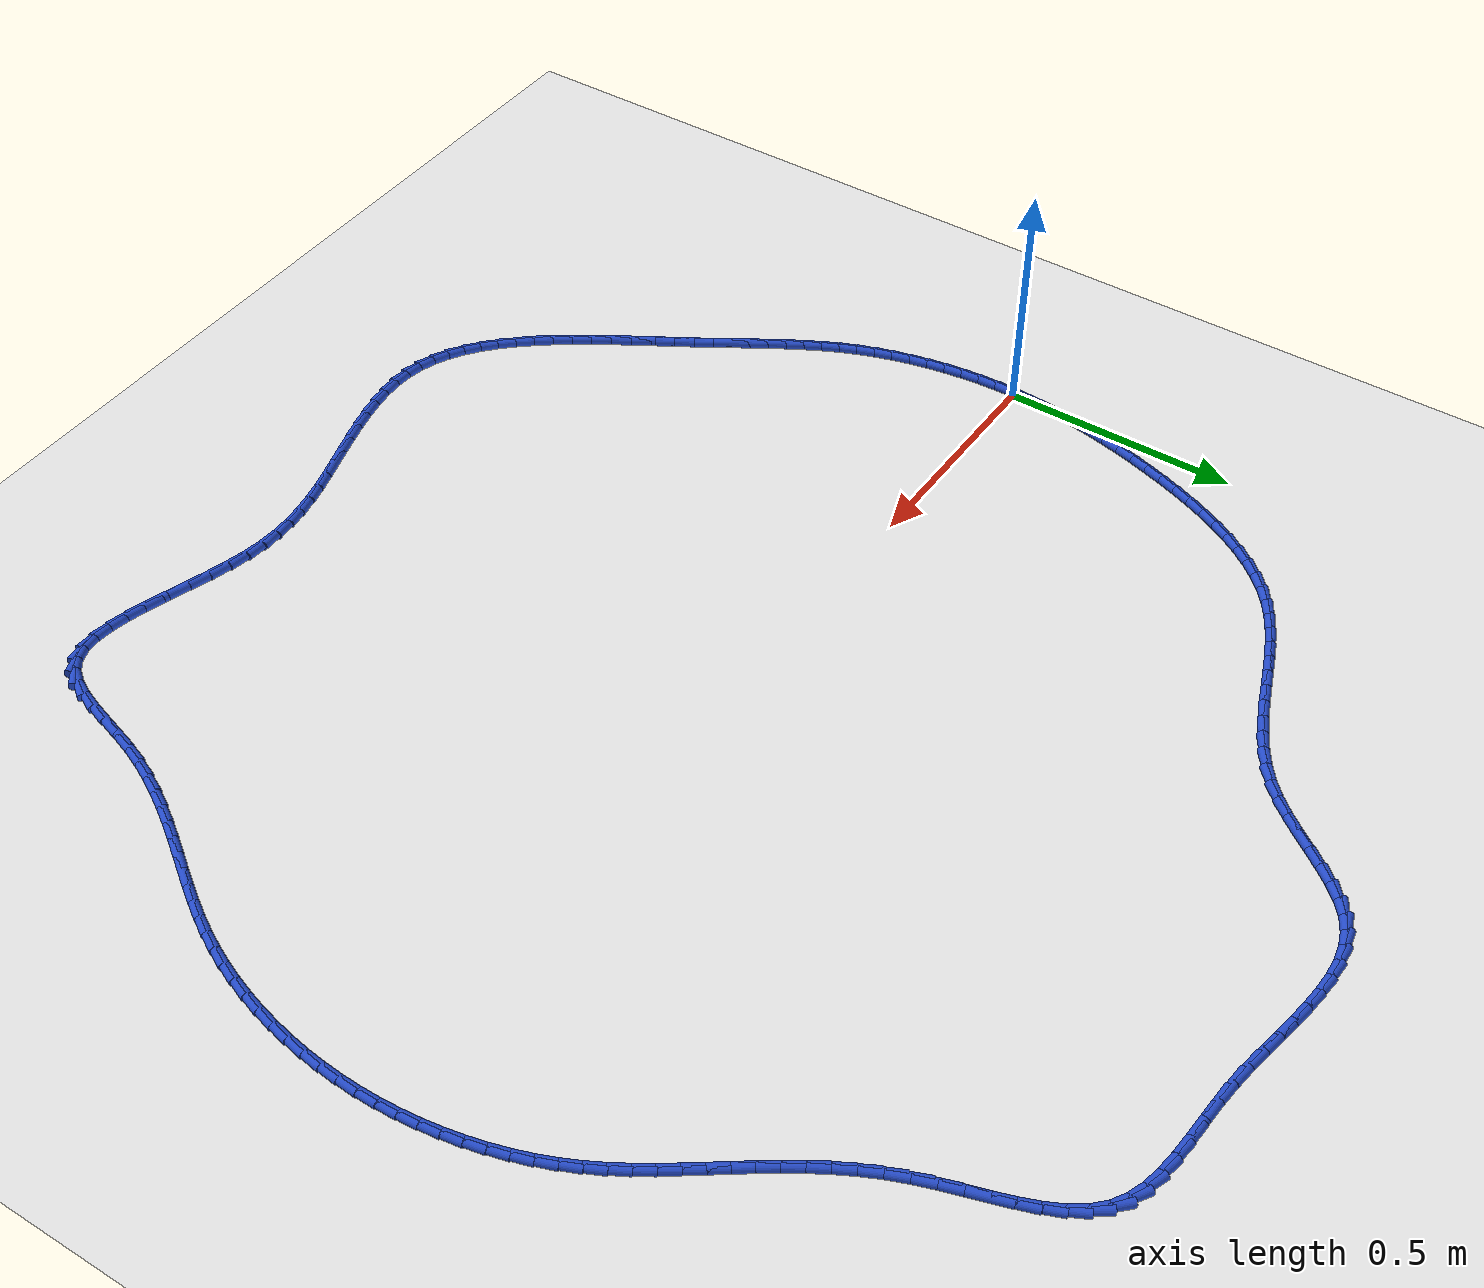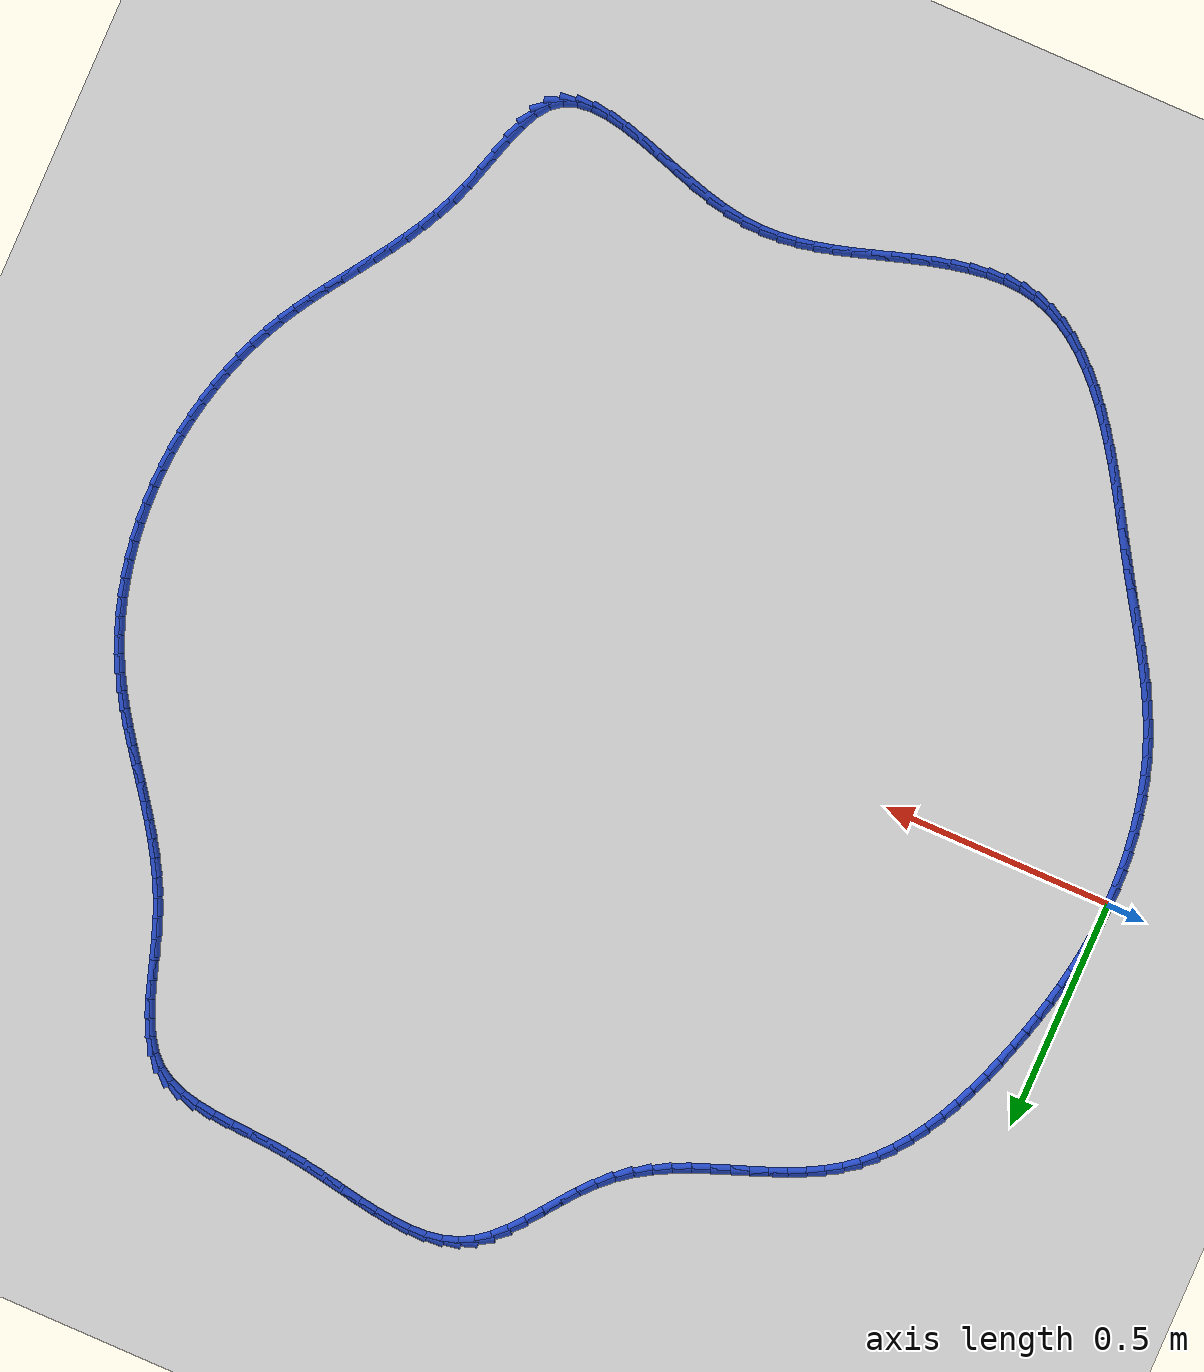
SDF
<sdf version="1.6">
 <world name="default">
  <light name="sun" type="directional">
   <pose>0 0 10 0 -0 0</pose>
   <diffuse>0.8 0.8 0.8 1</diffuse>
   <specular>0.2 0.2 0.2 1</specular>
   <attenuation>
    <range>1000</range>
    <constant>0.9</constant>
    <linear>0.01</linear>
    <quadratic>0.001</quadratic>
   </attenuation>
   <direction>-0.5 0.1 -0.9</direction>
  </light>
  <model name="ground_plane">
   <static>1</static>
   <link name="link">
    <collision name="collision">
     <geometry><plane><normal>0 0 1</normal><size>100 100</size></plane></geometry>
     <surface><friction><ode><mu>100</mu><mu2>50</mu2></ode></friction></surface>
    </collision>
    <visual name="visual">
     <cast_shadows>0</cast_shadows>
     <geometry><plane><normal>0 0 1</normal><size>100 100</size></plane></geometry>
     <material>
      <script><uri>file://media/materials/scripts/gazebo.material</uri><name>Gazebo/WhiteGlow</name></script>
     </material>
    </visual>
   </link>
  </model>
  <gravity>0 0 -9.8</gravity>
  <magnetic_field>6e-06 2.3e-05 -4.2e-05</magnetic_field>
  <atmosphere type="adiabatic"/>
  <physics name="default_physics" default="0" type="ode">
   <max_step_size>0.001</max_step_size>
   <real_time_factor>1</real_time_factor>
   <real_time_update_rate>1000</real_time_update_rate>
  </physics>
  <scene><ambient>0.4 0.4 0.4 1</ambient><background>0.7 0.7 0.7 1</background><shadows>1</shadows></scene>
  <spherical_coordinates>
   <surface_model>EARTH_WGS84</surface_model>
   <latitude_deg>0</latitude_deg>
   <longitude_deg>0</longitude_deg>
   <elevation>0</elevation>
   <heading_deg>0</heading_deg>
  </spherical_coordinates>
  <model name="line">
   <link name="link_0">
    <pose>1.214306433183765e-17 -4.163336342344337e-17 0.01 0 1.57 1.5359745579268451</pose>
    <collision name="collision">
     <geometry><cylinder><radius>0.01</radius><length>0.08</length></cylinder></geometry>
    </collision>
    <visual name="visual">
     <material>
      <script><name>Gazebo/Blue</name><uri>file://media/materials/scripts/gazebo.material</uri></script>
     </material>
     <geometry><cylinder><radius>0.01</radius><length>0.08</length></cylinder></geometry>
    </visual>
   </link>
   <link name="link_1">
    <pose>0.0013670674124619576 0.03924311899716643 0.01 0 1.57 1.4958907788421167</pose>
    <collision name="collision">
     <geometry><cylinder><radius>0.01</radius><length>0.08</length></cylinder></geometry>
    </collision>
    <visual name="visual">
     <material>
      <script><name>Gazebo/Blue</name><uri>file://media/materials/scripts/gazebo.material</uri></script>
     </material>
     <geometry><cylinder><radius>0.01</radius><length>0.08</length></cylinder></geometry>
    </visual>
   </link>
   <link name="link_2">
    <pose>0.004291375581555543 0.07821001698789096 0.01 0 1.57 1.457501562232395</pose>
    <collision name="collision">
     <geometry><cylinder><radius>0.01</radius><length>0.08</length></cylinder></geometry>
    </collision>
    <visual name="visual">
     <material>
      <script><name>Gazebo/Blue</name><uri>file://media/materials/scripts/gazebo.material</uri></script>
     </material>
     <geometry><cylinder><radius>0.01</radius><length>0.08</length></cylinder></geometry>
    </visual>
   </link>
   <link name="link_3">
    <pose>0.008700508661983042 0.11696072324996809 0.01 0 1.57 1.4210864554015243</pose>
    <collision name="collision">
     <geometry><cylinder><radius>0.01</radius><length>0.08</length></cylinder></geometry>
    </collision>
    <visual name="visual">
     <material>
      <script><name>Gazebo/Blue</name><uri>file://media/materials/scripts/gazebo.material</uri></script>
     </material>
     <geometry><cylinder><radius>0.01</radius><length>0.08</length></cylinder></geometry>
    </visual>
   </link>
   <link name="link_4">
    <pose>0.014522050808446754 0.15555526706119238 0.01 0 1.57 1.3868769630578819</pose>
    <collision name="collision">
     <geometry><cylinder><radius>0.01</radius><length>0.08</length></cylinder></geometry>
    </collision>
    <visual name="visual">
     <material>
      <script><name>Gazebo/Blue</name><uri>file://media/materials/scripts/gazebo.material</uri></script>
     </material>
     <geometry><cylinder><radius>0.01</radius><length>0.08</length></cylinder></geometry>
    </visual>
   </link>
   <link name="link_5">
    <pose>0.02168358617564896 0.19405367769935844 0.01 0 1.57 1.3550544888897538</pose>
    <collision name="collision">
     <geometry><cylinder><radius>0.01</radius><length>0.08</length></cylinder></geometry>
    </collision>
    <visual name="visual">
     <material>
      <script><name>Gazebo/Blue</name><uri>file://media/materials/scripts/gazebo.material</uri></script>
     </material>
     <geometry><cylinder><radius>0.01</radius><length>0.08</length></cylinder></geometry>
    </visual>
   </link>
   <link name="link_6">
    <pose>0.030112698918291936 0.23251598444226076 0.01 0 1.57 1.325751239393104</pose>
    <collision name="collision">
     <geometry><cylinder><radius>0.01</radius><length>0.08</length></cylinder></geometry>
    </collision>
    <visual name="visual">
     <material>
      <script><name>Gazebo/Blue</name><uri>file://media/materials/scripts/gazebo.material</uri></script>
     </material>
     <geometry><cylinder><radius>0.01</radius><length>0.08</length></cylinder></geometry>
    </visual>
   </link>
   <link name="link_7">
    <pose>0.039736973191077996 0.2710022165676941 0.01 0 1.57 1.2990534518479906</pose>
    <collision name="collision">
     <geometry><cylinder><radius>0.01</radius><length>0.08</length></cylinder></geometry>
    </collision>
    <visual name="visual">
     <material>
      <script><name>Gazebo/Blue</name><uri>file://media/materials/scripts/gazebo.material</uri></script>
     </material>
     <geometry><cylinder><radius>0.01</radius><length>0.08</length></cylinder></geometry>
    </visual>
   </link>
   <link name="link_8">
    <pose>0.0504839931487094 0.30957240335345276 0.01 0 1.57 1.2750011313172676</pose>
    <collision name="collision">
     <geometry><cylinder><radius>0.01</radius><length>0.08</length></cylinder></geometry>
    </collision>
    <visual name="visual">
     <material>
      <script><name>Gazebo/Blue</name><uri>file://media/materials/scripts/gazebo.material</uri></script>
     </material>
     <geometry><cylinder><radius>0.01</radius><length>0.08</length></cylinder></geometry>
    </visual>
   </link>
   <link name="link_9">
    <pose>0.06228148042419873 0.3482863198934669 0.01 0 1.57 1.2517160915492758</pose>
    <collision name="collision">
     <geometry><cylinder><radius>0.01</radius><length>0.08</length></cylinder></geometry>
    </collision>
    <visual name="visual">
     <material>
      <script><name>Gazebo/Blue</name><uri>file://media/materials/scripts/gazebo.material</uri></script>
     </material>
     <geometry><cylinder><radius>0.01</radius><length>0.08</length></cylinder></geometry>
    </visual>
   </link>
   <link name="link_10">
    <pose>0.07510770927820831 0.38711027444879925 0.01 0 1.57 1.224357988568602</pose>
    <collision name="collision">
     <geometry><cylinder><radius>0.01</radius><length>0.08</length></cylinder></geometry>
    </collision>
    <visual name="visual">
     <material>
      <script><name>Gazebo/Blue</name><uri>file://media/materials/scripts/gazebo.material</uri></script>
     </material>
     <geometry><cylinder><radius>0.01</radius><length>0.08</length></cylinder></geometry>
    </visual>
   </link>
   <link name="link_11">
    <pose>0.08906669449681354 0.42577809342506967 0.01 0 1.57 1.1918479280093806</pose>
    <collision name="collision">
     <geometry><cylinder><radius>0.01</radius><length>0.08</length></cylinder></geometry>
    </collision>
    <visual name="visual">
     <material>
      <script><name>Gazebo/Blue</name><uri>file://media/materials/scripts/gazebo.material</uri></script>
     </material>
     <geometry><cylinder><radius>0.01</radius><length>0.08</length></cylinder></geometry>
    </visual>
   </link>
   <link name="link_12">
    <pose>0.10428167143485165 0.4639880662880472 0.01 0 1.57 1.1536969208143462</pose>
    <collision name="collision">
     <geometry><cylinder><radius>0.01</radius><length>0.08</length></cylinder></geometry>
    </collision>
    <visual name="visual">
     <material>
      <script><name>Gazebo/Blue</name><uri>file://media/materials/scripts/gazebo.material</uri></script>
     </material>
     <geometry><cylinder><radius>0.01</radius><length>0.08</length></cylinder></geometry>
    </visual>
   </link>
   <link name="link_13">
    <pose>0.12087587544716 0.5014384825035014 0.01 0 1.57 1.1093035010048757</pose>
    <collision name="collision">
     <geometry><cylinder><radius>0.01</radius><length>0.08</length></cylinder></geometry>
    </collision>
    <visual name="visual">
     <material>
      <script><name>Gazebo/Blue</name><uri>file://media/materials/scripts/gazebo.material</uri></script>
     </material>
     <geometry><cylinder><radius>0.01</radius><length>0.08</length></cylinder></geometry>
    </visual>
   </link>
   <link name="link_14">
    <pose>0.1389725418885757 0.5378276315372013 0.01 0 1.57 1.0579701176258907</pose>
    <collision name="collision">
     <geometry><cylinder><radius>0.01</radius><length>0.08</length></cylinder></geometry>
    </collision>
    <visual name="visual">
     <material>
      <script><name>Gazebo/Blue</name><uri>file://media/materials/scripts/gazebo.material</uri></script>
     </material>
     <geometry><cylinder><radius>0.01</radius><length>0.08</length></cylinder></geometry>
    </visual>
   </link>
   <link name="link_15">
    <pose>0.15869490611393602 0.572853802854916 0.01 0 1.57 0.9989366385932948</pose>
    <collision name="collision">
     <geometry><cylinder><radius>0.01</radius><length>0.08</length></cylinder></geometry>
    </collision>
    <visual name="visual">
     <material>
      <script><name>Gazebo/Blue</name><uri>file://media/materials/scripts/gazebo.material</uri></script>
     </material>
     <geometry><cylinder><radius>0.01</radius><length>0.08</length></cylinder></geometry>
    </visual>
   </link>
   <link name="link_16">
    <pose>0.1801662034780783 0.6062152859224151 0.01 0 1.57 0.9314431742263272</pose>
    <collision name="collision">
     <geometry><cylinder><radius>0.01</radius><length>0.08</length></cylinder></geometry>
    </collision>
    <visual name="visual">
     <material>
      <script><name>Gazebo/Blue</name><uri>file://media/materials/scripts/gazebo.material</uri></script>
     </material>
     <geometry><cylinder><radius>0.01</radius><length>0.08</length></cylinder></geometry>
    </visual>
   </link>
   <link name="link_17">
    <pose>0.20350966933583967 0.6376103702054678 0.01 0 1.57 0.8548364505420084</pose>
    <collision name="collision">
     <geometry><cylinder><radius>0.01</radius><length>0.08</length></cylinder></geometry>
    </collision>
    <visual name="visual">
     <material>
      <script><name>Gazebo/Blue</name><uri>file://media/materials/scripts/gazebo.material</uri></script>
     </material>
     <geometry><cylinder><radius>0.01</radius><length>0.08</length></cylinder></geometry>
    </visual>
   </link>
   <link name="link_18">
    <pose>0.2288485390420575 0.6667373451698434 0.01 0 1.57 0.7687310149127787</pose>
    <collision name="collision">
     <geometry><cylinder><radius>0.01</radius><length>0.08</length></cylinder></geometry>
    </collision>
    <visual name="visual">
     <material>
      <script><name>Gazebo/Blue</name><uri>file://media/materials/scripts/gazebo.material</uri></script>
     </material>
     <geometry><cylinder><radius>0.01</radius><length>0.08</length></cylinder></geometry>
    </visual>
   </link>
   <link name="link_19">
    <pose>0.2563060479515689 0.693294500281311 0.01 0 1.57 0.6732660874902245</pose>
    <collision name="collision">
     <geometry><cylinder><radius>0.01</radius><length>0.08</length></cylinder></geometry>
    </collision>
    <visual name="visual">
     <material>
      <script><name>Gazebo/Blue</name><uri>file://media/materials/scripts/gazebo.material</uri></script>
     </material>
     <geometry><cylinder><radius>0.01</radius><length>0.08</length></cylinder></geometry>
    </visual>
   </link>
   <link name="link_20">
    <pose>0.28600457537489227 0.7169815731609596 0.01 0 1.57 0.576838897761728</pose>
    <collision name="collision">
     <geometry><cylinder><radius>0.01</radius><length>0.08</length></cylinder></geometry>
    </collision>
    <visual name="visual">
     <material>
      <script><name>Gazebo/Blue</name><uri>file://media/materials/scripts/gazebo.material</uri></script>
     </material>
     <geometry><cylinder><radius>0.01</radius><length>0.08</length></cylinder></geometry>
    </visual>
   </link>
   <link name="link_21">
    <pose>0.3179193500844083 0.7377472334417822 0.01 0 1.57 0.4968217438743447</pose>
    <collision name="collision">
     <geometry><cylinder><radius>0.01</radius><length>0.08</length></cylinder></geometry>
    </collision>
    <visual name="visual">
     <material>
      <script><name>Gazebo/Blue</name><uri>file://media/materials/scripts/gazebo.material</uri></script>
     </material>
     <geometry><cylinder><radius>0.01</radius><length>0.08</length></cylinder></geometry>
    </visual>
   </link>
   <link name="link_22">
    <pose>0.3517127322501112 0.7560694251423071 0.01 0 1.57 0.43554988571270187</pose>
    <collision name="collision">
     <geometry><cylinder><radius>0.01</radius><length>0.08</length></cylinder></geometry>
    </collision>
    <visual name="visual">
     <material>
      <script><name>Gazebo/Blue</name><uri>file://media/materials/scripts/gazebo.material</uri></script>
     </material>
     <geometry><cylinder><radius>0.01</radius><length>0.08</length></cylinder></geometry>
    </visual>
   </link>
   <link name="link_23">
    <pose>0.38700704337566716 0.7724938249981079 0.01 0 1.57 0.3924092793767784</pose>
    <collision name="collision">
     <geometry><cylinder><radius>0.01</radius><length>0.08</length></cylinder></geometry>
    </collision>
    <visual name="visual">
     <material>
      <script><name>Gazebo/Blue</name><uri>file://media/materials/scripts/gazebo.material</uri></script>
     </material>
     <geometry><cylinder><radius>0.01</radius><length>0.08</length></cylinder></geometry>
    </visual>
   </link>
   <link name="link_24">
    <pose>0.42342460496474243 0.787566109744759 0.01 0 1.57 0.36652514610684656</pose>
    <collision name="collision">
     <geometry><cylinder><radius>0.01</radius><length>0.08</length></cylinder></geometry>
    </collision>
    <visual name="visual">
     <material>
      <script><name>Gazebo/Blue</name><uri>file://media/materials/scripts/gazebo.material</uri></script>
     </material>
     <geometry><cylinder><radius>0.01</radius><length>0.08</length></cylinder></geometry>
    </visual>
   </link>
   <link name="link_25">
    <pose>0.46058773852100404 0.8018319561178348 0.01 0 1.57 0.35715670100760194</pose>
    <collision name="collision">
     <geometry><cylinder><radius>0.01</radius><length>0.08</length></cylinder></geometry>
    </collision>
    <visual name="visual">
     <material>
      <script><name>Gazebo/Blue</name><uri>file://media/materials/scripts/gazebo.material</uri></script>
     </material>
     <geometry><cylinder><radius>0.01</radius><length>0.08</length></cylinder></geometry>
    </visual>
   </link>
   <link name="link_26">
    <pose>0.49811876554811807 0.8158370408529088 0.01 0 1.57 0.36389035789225177</pose>
    <collision name="collision">
     <geometry><cylinder><radius>0.01</radius><length>0.08</length></cylinder></geometry>
    </collision>
    <visual name="visual">
     <material>
      <script><name>Gazebo/Blue</name><uri>file://media/materials/scripts/gazebo.material</uri></script>
     </material>
     <geometry><cylinder><radius>0.01</radius><length>0.08</length></cylinder></geometry>
    </visual>
   </link>
   <link name="link_27">
    <pose>0.5356400075497507 0.8301270406855555 0.01 0 1.57 0.38669128690416615</pose>
    <collision name="collision">
     <geometry><cylinder><radius>0.01</radius><length>0.08</length></cylinder></geometry>
    </collision>
    <visual name="visual">
     <material>
      <script><name>Gazebo/Blue</name><uri>file://media/materials/scripts/gazebo.material</uri></script>
     </material>
     <geometry><cylinder><radius>0.01</radius><length>0.08</length></cylinder></geometry>
    </visual>
   </link>
   <link name="link_28">
    <pose>0.5727737860295689 0.8452476323513488 0.01 0 1.57 0.42584471823210596</pose>
    <collision name="collision">
     <geometry><cylinder><radius>0.01</radius><length>0.08</length></cylinder></geometry>
    </collision>
    <visual name="visual">
     <material>
      <script><name>Gazebo/Blue</name><uri>file://media/materials/scripts/gazebo.material</uri></script>
     </material>
     <geometry><cylinder><radius>0.01</radius><length>0.08</length></cylinder></geometry>
    </visual>
   </link>
   <link name="link_29">
    <pose>0.6091424224912391 0.8617444925858635 0.01 0 1.57 0.48178208080744667</pose>
    <collision name="collision">
     <geometry><cylinder><radius>0.01</radius><length>0.08</length></cylinder></geometry>
    </collision>
    <visual name="visual">
     <material>
      <script><name>Gazebo/Blue</name><uri>file://media/materials/scripts/gazebo.material</uri></script>
     </material>
     <geometry><cylinder><radius>0.01</radius><length>0.08</length></cylinder></geometry>
    </visual>
   </link>
   <link name="link_30">
    <pose>0.6443682384384273 0.8801632981246731 0.01 0 1.57 0.5547627631440099</pose>
    <collision name="collision">
     <geometry><cylinder><radius>0.01</radius><length>0.08</length></cylinder></geometry>
    </collision>
    <visual name="visual">
     <material>
      <script><name>Gazebo/Blue</name><uri>file://media/materials/scripts/gazebo.material</uri></script>
     </material>
     <geometry><cylinder><radius>0.01</radius><length>0.08</length></cylinder></geometry>
    </visual>
   </link>
   <link name="link_31">
    <pose>0.6780735553748 0.9010497257033518 0.01 0 1.57 0.6443933276693075</pose>
    <collision name="collision">
     <geometry><cylinder><radius>0.01</radius><length>0.08</length></cylinder></geometry>
    </collision>
    <visual name="visual">
     <material>
      <script><name>Gazebo/Blue</name><uri>file://media/materials/scripts/gazebo.material</uri></script>
     </material>
     <geometry><cylinder><radius>0.01</radius><length>0.08</length></cylinder></geometry>
    </visual>
   </link>
   <link name="link_32">
    <pose>0.7098806948040239 0.9249494520574737 0.01 0 1.57 0.7476386784819729</pose>
    <collision name="collision">
     <geometry><cylinder><radius>0.01</radius><length>0.08</length></cylinder></geometry>
    </collision>
    <visual name="visual">
     <material>
      <script><name>Gazebo/Blue</name><uri>file://media/materials/scripts/gazebo.material</uri></script>
     </material>
     <geometry><cylinder><radius>0.01</radius><length>0.08</length></cylinder></geometry>
    </visual>
   </link>
   <link name="link_33">
    <pose>0.7394402083044123 0.9523568995657904 0.01 0 1.57 0.8371657122297678</pose>
    <collision name="collision">
     <geometry><cylinder><radius>0.01</radius><length>0.08</length></cylinder></geometry>
    </collision>
    <visual name="visual">
     <material>
      <script><name>Gazebo/Blue</name><uri>file://media/materials/scripts/gazebo.material</uri></script>
     </material>
     <geometry><cylinder><radius>0.01</radius><length>0.08</length></cylinder></geometry>
    </visual>
   </link>
   <link name="link_34">
    <pose>0.7669156300990237 0.9828351223465338 0.01 0 1.57 0.8930124837304063</pose>
    <collision name="collision">
     <geometry><cylinder><radius>0.01</radius><length>0.08</length></cylinder></geometry>
    </collision>
    <visual name="visual">
     <material>
      <script><name>Gazebo/Blue</name><uri>file://media/materials/scripts/gazebo.material</uri></script>
     </material>
     <geometry><cylinder><radius>0.01</radius><length>0.08</length></cylinder></geometry>
    </visual>
   </link>
   <link name="link_35">
    <pose>0.792917537380301 1.0151355259426207 0.01 0 1.57 0.9172627812410121</pose>
    <collision name="collision">
     <geometry><cylinder><radius>0.01</radius><length>0.08</length></cylinder></geometry>
    </collision>
    <visual name="visual">
     <material>
      <script><name>Gazebo/Blue</name><uri>file://media/materials/scripts/gazebo.material</uri></script>
     </material>
     <geometry><cylinder><radius>0.01</radius><length>0.08</length></cylinder></geometry>
    </visual>
   </link>
   <link name="link_36">
    <pose>0.8180714711706399 1.0479823476556671 0.01 0 1.57 0.9106997690434878</pose>
    <collision name="collision">
     <geometry><cylinder><radius>0.01</radius><length>0.08</length></cylinder></geometry>
    </collision>
    <visual name="visual">
     <material>
      <script><name>Gazebo/Blue</name><uri>file://media/materials/scripts/gazebo.material</uri></script>
     </material>
     <geometry><cylinder><radius>0.01</radius><length>0.08</length></cylinder></geometry>
    </visual>
   </link>
   <link name="link_37">
    <pose>0.8430029724924359 1.0800998247872886 0.01 0 1.57 0.8713539276780353</pose>
    <collision name="collision">
     <geometry><cylinder><radius>0.01</radius><length>0.08</length></cylinder></geometry>
    </collision>
    <visual name="visual">
     <material>
      <script><name>Gazebo/Blue</name><uri>file://media/materials/scripts/gazebo.material</uri></script>
     </material>
     <geometry><cylinder><radius>0.01</radius><length>0.08</length></cylinder></geometry>
    </visual>
   </link>
   <link name="link_38">
    <pose>0.8683375823680858 1.1102121946391024 0.01 0 1.57 0.7942003148657556</pose>
    <collision name="collision">
     <geometry><cylinder><radius>0.01</radius><length>0.08</length></cylinder></geometry>
    </collision>
    <visual name="visual">
     <material>
      <script><name>Gazebo/Blue</name><uri>file://media/materials/scripts/gazebo.material</uri></script>
     </material>
     <geometry><cylinder><radius>0.01</radius><length>0.08</length></cylinder></geometry>
    </visual>
   </link>
   <link name="link_39">
    <pose>0.8947008418199855 1.137043694512725 0.01 0 1.57 0.671706464112291</pose>
    <collision name="collision">
     <geometry><cylinder><radius>0.01</radius><length>0.08</length></cylinder></geometry>
    </collision>
    <visual name="visual">
     <material>
      <script><name>Gazebo/Blue</name><uri>file://media/materials/scripts/gazebo.material</uri></script>
     </material>
     <geometry><cylinder><radius>0.01</radius><length>0.08</length></cylinder></geometry>
    </visual>
   </link>
   <link name="link_40">
    <pose>0.9227182918705309 1.1593185617097717 0.01 0 1.57 0.5002158634046626</pose>
    <collision name="collision">
     <geometry><cylinder><radius>0.01</radius><length>0.08</length></cylinder></geometry>
    </collision>
    <visual name="visual">
     <material>
      <script><name>Gazebo/Blue</name><uri>file://media/materials/scripts/gazebo.material</uri></script>
     </material>
     <geometry><cylinder><radius>0.01</radius><length>0.08</length></cylinder></geometry>
    </visual>
   </link>
   <link name="link_41">
    <pose>0.9529761883646068 1.1758570077992336 0.01 0 1.57 0.31948546696179964</pose>
    <collision name="collision">
     <geometry><cylinder><radius>0.01</radius><length>0.08</length></cylinder></geometry>
    </collision>
    <visual name="visual">
     <material>
      <script><name>Gazebo/Blue</name><uri>file://media/materials/scripts/gazebo.material</uri></script>
     </material>
     <geometry><cylinder><radius>0.01</radius><length>0.08</length></cylinder></geometry>
    </visual>
   </link>
   <link name="link_42">
    <pose>0.9855839165107408 1.1866442463395734 0.01 0 1.57 0.16529931959805302</pose>
    <collision name="collision">
     <geometry><cylinder><radius>0.01</radius><length>0.08</length></cylinder></geometry>
    </collision>
    <visual name="visual">
     <material>
      <script><name>Gazebo/Blue</name><uri>file://media/materials/scripts/gazebo.material</uri></script>
     </material>
     <geometry><cylinder><radius>0.01</radius><length>0.08</length></cylinder></geometry>
    </visual>
   </link>
   <link name="link_43">
    <pose>1.020333341317882 1.192441197414258 0.01 0 1.57 0.04309647954061544</pose>
    <collision name="collision">
     <geometry><cylinder><radius>0.01</radius><length>0.08</length></cylinder></geometry>
    </collision>
    <visual name="visual">
     <material>
      <script><name>Gazebo/Blue</name><uri>file://media/materials/scripts/gazebo.material</uri></script>
     </material>
     <geometry><cylinder><radius>0.01</radius><length>0.08</length></cylinder></geometry>
    </visual>
   </link>
   <link name="link_44">
    <pose>1.0570105745523117 1.1940228363633438 0.01 0 1.57 -0.04837696851748006</pose>
    <collision name="collision">
     <geometry><cylinder><radius>0.01</radius><length>0.08</length></cylinder></geometry>
    </collision>
    <visual name="visual">
     <material>
      <script><name>Gazebo/Blue</name><uri>file://media/materials/scripts/gazebo.material</uri></script>
     </material>
     <geometry><cylinder><radius>0.01</radius><length>0.08</length></cylinder></geometry>
    </visual>
   </link>
   <link name="link_45">
    <pose>1.0954017279803103 1.1921641385268869 0.01 0 1.57 -0.11292749679227933</pose>
    <collision name="collision">
     <geometry><cylinder><radius>0.01</radius><length>0.08</length></cylinder></geometry>
    </collision>
    <visual name="visual">
     <material>
      <script><name>Gazebo/Blue</name><uri>file://media/materials/scripts/gazebo.material</uri></script>
     </material>
     <geometry><cylinder><radius>0.01</radius><length>0.08</length></cylinder></geometry>
    </visual>
   </link>
   <link name="link_46">
    <pose>1.13529291336816 1.187640079244943 0.01 0 1.57 -0.15453414171731195</pose>
    <collision name="collision">
     <geometry><cylinder><radius>0.01</radius><length>0.08</length></cylinder></geometry>
    </collision>
    <visual name="visual">
     <material>
      <script><name>Gazebo/Blue</name><uri>file://media/materials/scripts/gazebo.material</uri></script>
     </material>
     <geometry><cylinder><radius>0.01</radius><length>0.08</length></cylinder></geometry>
    </visual>
   </link>
   <link name="link_47">
    <pose>1.176470242482141 1.1812256338575697 0.01 0 1.57 -0.1763713679223576</pose>
    <collision name="collision">
     <geometry><cylinder><radius>0.01</radius><length>0.08</length></cylinder></geometry>
    </collision>
    <visual name="visual">
     <material>
      <script><name>Gazebo/Blue</name><uri>file://media/materials/scripts/gazebo.material</uri></script>
     </material>
     <geometry><cylinder><radius>0.01</radius><length>0.08</length></cylinder></geometry>
    </visual>
   </link>
   <link name="link_48">
    <pose>1.2187198270885347 1.1736957777048223 0.01 0 1.57 -0.18058279782413014</pose>
    <collision name="collision">
     <geometry><cylinder><radius>0.01</radius><length>0.08</length></cylinder></geometry>
    </collision>
    <visual name="visual">
     <material>
      <script><name>Gazebo/Blue</name><uri>file://media/materials/scripts/gazebo.material</uri></script>
     </material>
     <geometry><cylinder><radius>0.01</radius><length>0.08</length></cylinder></geometry>
    </visual>
   </link>
   <link name="link_49">
    <pose>1.2618277789536232 1.165825486126757 0.01 0 1.57 -0.1683421394747414</pose>
    <collision name="collision">
     <geometry><cylinder><radius>0.01</radius><length>0.08</length></cylinder></geometry>
    </collision>
    <visual name="visual">
     <material>
      <script><name>Gazebo/Blue</name><uri>file://media/materials/scripts/gazebo.material</uri></script>
     </material>
     <geometry><cylinder><radius>0.01</radius><length>0.08</length></cylinder></geometry>
    </visual>
   </link>
   <link name="link_50">
    <pose>1.305580209843687 1.1583897344634313 0.01 0 1.57 -0.13999736501508236</pose>
    <collision name="collision">
     <geometry><cylinder><radius>0.01</radius><length>0.08</length></cylinder></geometry>
    </collision>
    <visual name="visual">
     <material>
      <script><name>Gazebo/Blue</name><uri>file://media/materials/scripts/gazebo.material</uri></script>
     </material>
     <geometry><cylinder><radius>0.01</radius><length>0.08</length></cylinder></geometry>
    </visual>
   </link>
   <link name="link_51">
    <pose>1.3497632315250065 1.1521634980549003 0.01 0 1.57 -0.09769345975118965</pose>
    <collision name="collision">
     <geometry><cylinder><radius>0.01</radius><length>0.08</length></cylinder></geometry>
    </collision>
    <visual name="visual">
     <material>
      <script><name>Gazebo/Blue</name><uri>file://media/materials/scripts/gazebo.material</uri></script>
     </material>
     <geometry><cylinder><radius>0.01</radius><length>0.08</length></cylinder></geometry>
    </visual>
   </link>
   <link name="link_52">
    <pose>1.3941388752463069 1.1478144432693274 0.01 0 1.57 -0.06612649248069756</pose>
    <collision name="collision">
     <geometry><cylinder><radius>0.01</radius><length>0.08</length></cylinder></geometry>
    </collision>
    <visual name="visual">
     <material>
      <script><name>Gazebo/Blue</name><uri>file://media/materials/scripts/gazebo.material</uri></script>
     </material>
     <geometry><cylinder><radius>0.01</radius><length>0.08</length></cylinder></geometry>
    </visual>
   </link>
   <link name="link_53">
    <pose>1.438218981985006 1.1448953243585869 0.01 0 1.57 -0.06012502095473905</pose>
    <collision name="collision">
     <geometry><cylinder><radius>0.01</radius><length>0.08</length></cylinder></geometry>
    </collision>
    <visual name="visual">
     <material>
      <script><name>Gazebo/Blue</name><uri>file://media/materials/scripts/gazebo.material</uri></script>
     </material>
     <geometry><cylinder><radius>0.01</radius><length>0.08</length></cylinder></geometry>
    </visual>
   </link>
   <link name="link_54">
    <pose>1.4813670661412666 1.14229791424507 0.01 0 1.57 -0.08141634280745495</pose>
    <collision name="collision">
     <geometry><cylinder><radius>0.01</radius><length>0.08</length></cylinder></geometry>
    </collision>
    <visual name="visual">
     <material>
      <script><name>Gazebo/Blue</name><uri>file://media/materials/scripts/gazebo.material</uri></script>
     </material>
     <geometry><cylinder><radius>0.01</radius><length>0.08</length></cylinder></geometry>
    </visual>
   </link>
   <link name="link_55">
    <pose>1.5229446966216837 1.1389053162320786 0.01 0 1.57 -0.13393681096609522</pose>
    <collision name="collision">
     <geometry><cylinder><radius>0.01</radius><length>0.08</length></cylinder></geometry>
    </collision>
    <visual name="visual">
     <material>
      <script><name>Gazebo/Blue</name><uri>file://media/materials/scripts/gazebo.material</uri></script>
     </material>
     <geometry><cylinder><radius>0.01</radius><length>0.08</length></cylinder></geometry>
    </visual>
   </link>
   <link name="link_56">
    <pose>1.5623134423328493 1.1336006336229134 0.01 0 1.57 -0.22434445334545514</pose>
    <collision name="collision">
     <geometry><cylinder><radius>0.01</radius><length>0.08</length></cylinder></geometry>
    </collision>
    <visual name="visual">
     <material>
      <script><name>Gazebo/Blue</name><uri>file://media/materials/scripts/gazebo.material</uri></script>
     </material>
     <geometry><cylinder><radius>0.01</radius><length>0.08</length></cylinder></geometry>
    </visual>
   </link>
   <link name="link_57">
    <pose>1.598834872181358 1.1252669697208761 0.01 0 1.57 -0.36118772963823204</pose>
    <collision name="collision">
     <geometry><cylinder><radius>0.01</radius><length>0.08</length></cylinder></geometry>
    </collision>
    <visual name="visual">
     <material>
      <script><name>Gazebo/Blue</name><uri>file://media/materials/scripts/gazebo.material</uri></script>
     </material>
     <geometry><cylinder><radius>0.01</radius><length>0.08</length></cylinder></geometry>
    </visual>
   </link>
   <link name="link_58">
    <pose>1.6318705550738042 1.1127874278292682 0.01 0 1.57 -0.5504152419705859</pose>
    <collision name="collision">
     <geometry><cylinder><radius>0.01</radius><length>0.08</length></cylinder></geometry>
    </collision>
    <visual name="visual">
     <material>
      <script><name>Gazebo/Blue</name><uri>file://media/materials/scripts/gazebo.material</uri></script>
     </material>
     <geometry><cylinder><radius>0.01</radius><length>0.08</length></cylinder></geometry>
    </visual>
   </link>
   <link name="link_59">
    <pose>1.66078205991678 1.0950451112513901 0.01 0 1.57 -0.7734066583830509</pose>
    <collision name="collision">
     <geometry><cylinder><radius>0.01</radius><length>0.08</length></cylinder></geometry>
    </collision>
    <visual name="visual">
     <material>
      <script><name>Gazebo/Blue</name><uri>file://media/materials/scripts/gazebo.material</uri></script>
     </material>
     <geometry><cylinder><radius>0.01</radius><length>0.08</length></cylinder></geometry>
    </visual>
   </link>
   <link name="link_60">
    <pose>1.685156433288459 1.0712484092607149 0.01 0 1.57 -0.9609246988969561</pose>
    <collision name="collision">
     <geometry><cylinder><radius>0.01</radius><length>0.08</length></cylinder></geometry>
    </collision>
    <visual name="visual">
     <material>
      <script><name>Gazebo/Blue</name><uri>file://media/materials/scripts/gazebo.material</uri></script>
     </material>
     <geometry><cylinder><radius>0.01</radius><length>0.08</length></cylinder></geometry>
    </visual>
   </link>
   <link name="link_61">
    <pose>1.705570062022927 1.0420329855154473 0.01 0 1.57 -1.0953885970075545</pose>
    <collision name="collision">
     <geometry><cylinder><radius>0.01</radius><length>0.08</length></cylinder></geometry>
    </collision>
    <visual name="visual">
     <material>
      <script><name>Gazebo/Blue</name><uri>file://media/materials/scripts/gazebo.material</uri></script>
     </material>
     <geometry><cylinder><radius>0.01</radius><length>0.08</length></cylinder></geometry>
    </visual>
   </link>
   <link name="link_62">
    <pose>1.7228706034601493 1.0084258527997005 0.01 0 1.57 -1.1845580967819753</pose>
    <collision name="collision">
     <geometry><cylinder><radius>0.01</radius><length>0.08</length></cylinder></geometry>
    </collision>
    <visual name="visual">
     <material>
      <script><name>Gazebo/Blue</name><uri>file://media/materials/scripts/gazebo.material</uri></script>
     </material>
     <geometry><cylinder><radius>0.01</radius><length>0.08</length></cylinder></geometry>
    </visual>
   </link>
   <link name="link_63">
    <pose>1.7379057221938086 0.9714540343621788 0.01 0 1.57 -1.2373195886929786</pose>
    <collision name="collision">
     <geometry><cylinder><radius>0.01</radius><length>0.08</length></cylinder></geometry>
    </collision>
    <visual name="visual">
     <material>
      <script><name>Gazebo/Blue</name><uri>file://media/materials/scripts/gazebo.material</uri></script>
     </material>
     <geometry><cylinder><radius>0.01</radius><length>0.08</length></cylinder></geometry>
    </visual>
   </link>
   <link name="link_64">
    <pose>1.751523082817585 0.9321445534515873 0.01 0 1.57 -1.2600033414593645</pose>
    <collision name="collision">
     <geometry><cylinder><radius>0.01</radius><length>0.08</length></cylinder></geometry>
    </collision>
    <visual name="visual">
     <material>
      <script><name>Gazebo/Blue</name><uri>file://media/materials/scripts/gazebo.material</uri></script>
     </material>
     <geometry><cylinder><radius>0.01</radius><length>0.08</length></cylinder></geometry>
    </visual>
   </link>
   <link name="link_65">
    <pose>1.7645703499251606 0.89152443331663 0.01 0 1.57 -1.2558763671386122</pose>
    <collision name="collision">
     <geometry><cylinder><radius>0.01</radius><length>0.08</length></cylinder></geometry>
    </collision>
    <visual name="visual">
     <material>
      <script><name>Gazebo/Blue</name><uri>file://media/materials/scripts/gazebo.material</uri></script>
     </material>
     <geometry><cylinder><radius>0.01</radius><length>0.08</length></cylinder></geometry>
    </visual>
   </link>
   <link name="link_66">
    <pose>1.7778951881102159 0.8506206972060109 0.01 0 1.57 -1.225409267560163</pose>
    <collision name="collision">
     <geometry><cylinder><radius>0.01</radius><length>0.08</length></cylinder></geometry>
    </collision>
    <visual name="visual">
     <material>
      <script><name>Gazebo/Blue</name><uri>file://media/materials/scripts/gazebo.material</uri></script>
     </material>
     <geometry><cylinder><radius>0.01</radius><length>0.08</length></cylinder></geometry>
    </visual>
   </link>
   <link name="link_67">
    <pose>1.7923452619664322 0.8104603683684354 0.01 0 1.57 -1.1698681735073404</pose>
    <collision name="collision">
     <geometry><cylinder><radius>0.01</radius><length>0.08</length></cylinder></geometry>
    </collision>
    <visual name="visual">
     <material>
      <script><name>Gazebo/Blue</name><uri>file://media/materials/scripts/gazebo.material</uri></script>
     </material>
     <geometry><cylinder><radius>0.01</radius><length>0.08</length></cylinder></geometry>
    </visual>
   </link>
   <link name="link_68">
    <pose>1.8086661027960687 0.7719576226477841 0.01 0 1.57 -1.1106709265701271</pose>
    <collision name="collision">
     <geometry><cylinder><radius>0.01</radius><length>0.08</length></cylinder></geometry>
    </collision>
    <visual name="visual">
     <material>
      <script><name>Gazebo/Blue</name><uri>file://media/materials/scripts/gazebo.material</uri></script>
     </material>
     <geometry><cylinder><radius>0.01</radius><length>0.08</length></cylinder></geometry>
    </visual>
   </link>
   <link name="link_69">
    <pose>1.8268733588061365 0.7352201856896173 0.01 0 1.57 -1.058772264885773</pose>
    <collision name="collision">
     <geometry><cylinder><radius>0.01</radius><length>0.08</length></cylinder></geometry>
    </collision>
    <visual name="visual">
     <material>
      <script><name>Gazebo/Blue</name><uri>file://media/materials/scripts/gazebo.material</uri></script>
     </material>
     <geometry><cylinder><radius>0.01</radius><length>0.08</length></cylinder></geometry>
    </visual>
   </link>
   <link name="link_70">
    <pose>1.8466650550471124 0.7000048402840624 0.01 0 1.57 -1.0151336223634433</pose>
    <collision name="collision">
     <geometry><cylinder><radius>0.01</radius><length>0.08</length></cylinder></geometry>
    </collision>
    <visual name="visual">
     <material>
      <script><name>Gazebo/Blue</name><uri>file://media/materials/scripts/gazebo.material</uri></script>
     </material>
     <geometry><cylinder><radius>0.01</radius><length>0.08</length></cylinder></geometry>
    </visual>
   </link>
   <link name="link_71">
    <pose>1.8677379112720736 0.6660669269939165 0.01 0 1.57 -0.9803995666466075</pose>
    <collision name="collision">
     <geometry><cylinder><radius>0.01</radius><length>0.08</length></cylinder></geometry>
    </collision>
    <visual name="visual">
     <material>
      <script><name>Gazebo/Blue</name><uri>file://media/materials/scripts/gazebo.material</uri></script>
     </material>
     <geometry><cylinder><radius>0.01</radius><length>0.08</length></cylinder></geometry>
    </visual>
   </link>
   <link name="link_72">
    <pose>1.889788647234098 0.6331617863819781 0.01 0 1.57 -0.955001847810761</pose>
    <collision name="collision">
     <geometry><cylinder><radius>0.01</radius><length>0.08</length></cylinder></geometry>
    </collision>
    <visual name="visual">
     <material>
      <script><name>Gazebo/Blue</name><uri>file://media/materials/scripts/gazebo.material</uri></script>
     </material>
     <geometry><cylinder><radius>0.01</radius><length>0.08</length></cylinder></geometry>
    </visual>
   </link>
   <link name="link_73">
    <pose>1.9125139826862616 0.6010447590110448 0.01 0 1.57 -0.9392286483356797</pose>
    <collision name="collision">
     <geometry><cylinder><radius>0.01</radius><length>0.08</length></cylinder></geometry>
    </collision>
    <visual name="visual">
     <material>
      <script><name>Gazebo/Blue</name><uri>file://media/materials/scripts/gazebo.material</uri></script>
     </material>
     <geometry><cylinder><radius>0.01</radius><length>0.08</length></cylinder></geometry>
    </visual>
   </link>
   <link name="link_74">
    <pose>1.9356106373816433 0.5694711854439144 0.01 0 1.57 -0.9332848872651573</pose>
    <collision name="collision">
     <geometry><cylinder><radius>0.01</radius><length>0.08</length></cylinder></geometry>
    </collision>
    <visual name="visual">
     <material>
      <script><name>Gazebo/Blue</name><uri>file://media/materials/scripts/gazebo.material</uri></script>
     </material>
     <geometry><cylinder><radius>0.01</radius><length>0.08</length></cylinder></geometry>
    </visual>
   </link>
   <link name="link_75">
    <pose>1.9587753310733191 0.5381964062433853 0.01 0 1.57 -0.9373331607517976</pose>
    <collision name="collision">
     <geometry><cylinder><radius>0.01</radius><length>0.08</length></cylinder></geometry>
    </collision>
    <visual name="visual">
     <material>
      <script><name>Gazebo/Blue</name><uri>file://media/materials/scripts/gazebo.material</uri></script>
     </material>
     <geometry><cylinder><radius>0.01</radius><length>0.08</length></cylinder></geometry>
    </visual>
   </link>
   <link name="link_76">
    <pose>1.9817047835143666 0.5069757619722548 0.01 0 1.57 -0.9515091542326454</pose>
    <collision name="collision">
     <geometry><cylinder><radius>0.01</radius><length>0.08</length></cylinder></geometry>
    </collision>
    <visual name="visual">
     <material>
      <script><name>Gazebo/Blue</name><uri>file://media/materials/scripts/gazebo.material</uri></script>
     </material>
     <geometry><cylinder><radius>0.01</radius><length>0.08</length></cylinder></geometry>
    </visual>
   </link>
   <link name="link_77">
    <pose>2.004095714457862 0.47556459319332045 0.01 0 1.57 -0.9759076475280166</pose>
    <collision name="collision">
     <geometry><cylinder><radius>0.01</radius><length>0.08</length></cylinder></geometry>
    </collision>
    <visual name="visual">
     <material>
      <script><name>Gazebo/Blue</name><uri>file://media/materials/scripts/gazebo.material</uri></script>
     </material>
     <geometry><cylinder><radius>0.01</radius><length>0.08</length></cylinder></geometry>
    </visual>
   </link>
   <link name="link_78">
    <pose>2.0256448436568846 0.4437182404693811 0.01 0 1.57 -1.0105367489064634</pose>
    <collision name="collision">
     <geometry><cylinder><radius>0.01</radius><length>0.08</length></cylinder></geometry>
    </collision>
    <visual name="visual">
     <material>
      <script><name>Gazebo/Blue</name><uri>file://media/materials/scripts/gazebo.material</uri></script>
     </material>
     <geometry><cylinder><radius>0.01</radius><length>0.08</length></cylinder></geometry>
    </visual>
   </link>
   <link name="link_79">
    <pose>2.04604889086451 0.41119204436323403 0.01 0 1.57 -1.0552407817311305</pose>
    <collision name="collision">
     <geometry><cylinder><radius>0.01</radius><length>0.08</length></cylinder></geometry>
    </collision>
    <visual name="visual">
     <material>
      <script><name>Gazebo/Blue</name><uri>file://media/materials/scripts/gazebo.material</uri></script>
     </material>
     <geometry><cylinder><radius>0.01</radius><length>0.08</length></cylinder></geometry>
    </visual>
   </link>
   <link name="link_80">
    <pose>2.0650045758338154 0.3777413454376769 0.01 0 1.57 -1.1088319563055218</pose>
    <collision name="collision">
     <geometry><cylinder><radius>0.01</radius><length>0.08</length></cylinder></geometry>
    </collision>
    <visual name="visual">
     <material>
      <script><name>Gazebo/Blue</name><uri>file://media/materials/scripts/gazebo.material</uri></script>
     </material>
     <geometry><cylinder><radius>0.01</radius><length>0.08</length></cylinder></geometry>
    </visual>
   </link>
   <link name="link_81">
    <pose>2.0822292402647444 0.34314656067190424 0.01 0 1.57 -1.163944920681932</pose>
    <collision name="collision">
     <geometry><cylinder><radius>0.01</radius><length>0.08</length></cylinder></geometry>
    </collision>
    <visual name="visual">
     <material>
      <script><name>Gazebo/Blue</name><uri>file://media/materials/scripts/gazebo.material</uri></script>
     </material>
     <geometry><cylinder><radius>0.01</radius><length>0.08</length></cylinder></geometry>
    </visual>
   </link>
   <link name="link_82">
    <pose>2.0976260944583047 0.30741412442677196 0.01 0 1.57 -1.2170033602918657</pose>
    <collision name="collision">
     <geometry><cylinder><radius>0.01</radius><length>0.08</length></cylinder></geometry>
    </collision>
    <visual name="visual">
     <material>
      <script><name>Gazebo/Blue</name><uri>file://media/materials/scripts/gazebo.material</uri></script>
     </material>
     <geometry><cylinder><radius>0.01</radius><length>0.08</length></cylinder></geometry>
    </visual>
   </link>
   <link name="link_83">
    <pose>2.1111968252769664 0.27067021917792844 0.01 0 1.57 -1.2681919873966485</pose>
    <collision name="collision">
     <geometry><cylinder><radius>0.01</radius><length>0.08</length></cylinder></geometry>
    </collision>
    <visual name="visual">
     <material>
      <script><name>Gazebo/Blue</name><uri>file://media/materials/scripts/gazebo.material</uri></script>
     </material>
     <geometry><cylinder><radius>0.01</radius><length>0.08</length></cylinder></geometry>
    </visual>
   </link>
   <link name="link_84">
    <pose>2.1229440199665746 0.2330421222728375 0.01 0 1.57 -1.3177429510259306</pose>
    <collision name="collision">
     <geometry><cylinder><radius>0.01</radius><length>0.08</length></cylinder></geometry>
    </collision>
    <visual name="visual">
     <material>
      <script><name>Gazebo/Blue</name><uri>file://media/materials/scripts/gazebo.material</uri></script>
     </material>
     <geometry><cylinder><radius>0.01</radius><length>0.08</length></cylinder></geometry>
    </visual>
   </link>
   <link name="link_85">
    <pose>2.132870265772972 0.19465711105896188 0.01 0 1.57 -1.3658964082267315</pose>
    <collision name="collision">
     <geometry><cylinder><radius>0.01</radius><length>0.08</length></cylinder></geometry>
    </collision>
    <visual name="visual">
     <material>
      <script><name>Gazebo/Blue</name><uri>file://media/materials/scripts/gazebo.material</uri></script>
     </material>
     <geometry><cylinder><radius>0.01</radius><length>0.08</length></cylinder></geometry>
    </visual>
   </link>
   <link name="link_86">
    <pose>2.140978149942003 0.15564246288376546 0.01 0 1.57 -1.412896460306759</pose>
    <collision name="collision">
     <geometry><cylinder><radius>0.01</radius><length>0.08</length></cylinder></geometry>
    </collision>
    <visual name="visual">
     <material>
      <script><name>Gazebo/Blue</name><uri>file://media/materials/scripts/gazebo.material</uri></script>
     </material>
     <geometry><cylinder><radius>0.01</radius><length>0.08</length></cylinder></geometry>
    </visual>
   </link>
   <link name="link_87">
    <pose>2.1472702597195115 0.11612545509471123 0.01 0 1.57 -1.458988611674432</pose>
    <collision name="collision">
     <geometry><cylinder><radius>0.01</radius><length>0.08</length></cylinder></geometry>
    </collision>
    <visual name="visual">
     <material>
      <script><name>Gazebo/Blue</name><uri>file://media/materials/scripts/gazebo.material</uri></script>
     </material>
     <geometry><cylinder><radius>0.01</radius><length>0.08</length></cylinder></geometry>
    </visual>
   </link>
   <link name="link_88">
    <pose>2.1517491823513413 0.07623336503926202 0.01 0 1.57 -1.5044184082559038</pose>
    <collision name="collision">
     <geometry><cylinder><radius>0.01</radius><length>0.08</length></cylinder></geometry>
    </collision>
    <visual name="visual">
     <material>
      <script><name>Gazebo/Blue</name><uri>file://media/materials/scripts/gazebo.material</uri></script>
     </material>
     <geometry><cylinder><radius>0.01</radius><length>0.08</length></cylinder></geometry>
    </visual>
   </link>
   <link name="link_89">
    <pose>2.1544175050833356 0.03609347006488196 0.01 0 1.57 -1.5494058028002868</pose>
    <collision name="collision">
     <geometry><cylinder><radius>0.01</radius><length>0.08</length></cylinder></geometry>
    </collision>
    <visual name="visual">
     <material>
      <script><name>Gazebo/Blue</name><uri>file://media/materials/scripts/gazebo.material</uri></script>
     </material>
     <geometry><cylinder><radius>0.01</radius><length>0.08</length></cylinder></geometry>
    </visual>
   </link>
   <link name="link_90">
    <pose>2.1552788466413904 -0.004167824329971389 0.01 0 1.57 1.5477274742445282</pose>
    <collision name="collision">
     <geometry><cylinder><radius>0.01</radius><length>0.08</length></cylinder></geometry>
    </collision>
    <visual name="visual">
     <material>
      <script><name>Gazebo/Blue</name><uri>file://media/materials/scripts/gazebo.material</uri></script>
     </material>
     <geometry><cylinder><radius>0.01</radius><length>0.08</length></cylinder></geometry>
    </visual>
   </link>
   <link name="link_91">
    <pose>2.1543497631818864 -0.04443504789070137 0.01 0 1.57 1.503820248179985</pose>
    <collision name="collision">
     <geometry><cylinder><radius>0.01</radius><length>0.08</length></cylinder></geometry>
    </collision>
    <visual name="visual">
     <material>
      <script><name>Gazebo/Blue</name><uri>file://media/materials/scripts/gazebo.material</uri></script>
     </material>
     <geometry><cylinder><radius>0.01</radius><length>0.08</length></cylinder></geometry>
    </visual>
   </link>
   <link name="link_92">
    <pose>2.1516556301665863 -0.08460018479929013 0.01 0 1.57 1.460283164392499</pose>
    <collision name="collision">
     <geometry><cylinder><radius>0.01</radius><length>0.08</length></cylinder></geometry>
    </collision>
    <visual name="visual">
     <material>
      <script><name>Gazebo/Blue</name><uri>file://media/materials/scripts/gazebo.material</uri></script>
     </material>
     <geometry><cylinder><radius>0.01</radius><length>0.08</length></cylinder></geometry>
    </visual>
   </link>
   <link name="link_93">
    <pose>2.147221992813884 -0.12455536272294392 0.01 0 1.57 1.416926217196085</pose>
    <collision name="collision">
     <geometry><cylinder><radius>0.01</radius><length>0.08</length></cylinder></geometry>
    </collision>
    <visual name="visual">
     <material>
      <script><name>Gazebo/Blue</name><uri>file://media/materials/scripts/gazebo.material</uri></script>
     </material>
     <geometry><cylinder><radius>0.01</radius><length>0.08</length></cylinder></geometry>
    </visual>
   </link>
   <link name="link_94">
    <pose>2.1410743963421703 -0.16419270932887126 0.01 0 1.57 1.3735557055828278</pose>
    <collision name="collision">
     <geometry><cylinder><radius>0.01</radius><length>0.08</length></cylinder></geometry>
    </collision>
    <visual name="visual">
     <material>
      <script><name>Gazebo/Blue</name><uri>file://media/materials/scripts/gazebo.material</uri></script>
     </material>
     <geometry><cylinder><radius>0.01</radius><length>0.08</length></cylinder></geometry>
    </visual>
   </link>
   <link name="link_95">
    <pose>2.1332383859698396 -0.20340435228428005 0.01 0 1.57 1.3299741830995393</pose>
    <collision name="collision">
     <geometry><cylinder><radius>0.01</radius><length>0.08</length></cylinder></geometry>
    </collision>
    <visual name="visual">
     <material>
      <script><name>Gazebo/Blue</name><uri>file://media/materials/scripts/gazebo.material</uri></script>
     </material>
     <geometry><cylinder><radius>0.01</radius><length>0.08</length></cylinder></geometry>
    </visual>
   </link>
   <link name="link_96">
    <pose>2.1237395069152836 -0.24208241925637816 0.01 0 1.57 1.285980319600134</pose>
    <collision name="collision">
     <geometry><cylinder><radius>0.01</radius><length>0.08</length></cylinder></geometry>
    </collision>
    <visual name="visual">
     <material>
      <script><name>Gazebo/Blue</name><uri>file://media/materials/scripts/gazebo.material</uri></script>
     </material>
     <geometry><cylinder><radius>0.01</radius><length>0.08</length></cylinder></geometry>
    </visual>
   </link>
   <link name="link_97">
    <pose>2.112603304396896 -0.2801190379123733 0.01 0 1.57 1.2413688086549268</pose>
    <collision name="collision">
     <geometry><cylinder><radius>0.01</radius><length>0.08</length></cylinder></geometry>
    </collision>
    <visual name="visual">
     <material>
      <script><name>Gazebo/Blue</name><uri>file://media/materials/scripts/gazebo.material</uri></script>
     </material>
     <geometry><cylinder><radius>0.01</radius><length>0.08</length></cylinder></geometry>
    </visual>
   </link>
   <link name="link_98">
    <pose>2.099855323633068 -0.31740633591947415 0.01 0 1.57 1.1959304695225348</pose>
    <collision name="collision">
     <geometry><cylinder><radius>0.01</radius><length>0.08</length></cylinder></geometry>
    </collision>
    <visual name="visual">
     <material>
      <script><name>Gazebo/Blue</name><uri>file://media/materials/scripts/gazebo.material</uri></script>
     </material>
     <geometry><cylinder><radius>0.01</radius><length>0.08</length></cylinder></geometry>
    </visual>
   </link>
   <link name="link_99">
    <pose>2.085521109842194 -0.353836440944887 0.01 0 1.57 1.1494527156915364</pose>
    <collision name="collision">
     <geometry><cylinder><radius>0.01</radius><length>0.08</length></cylinder></geometry>
    </collision>
    <visual name="visual">
     <material>
      <script><name>Gazebo/Blue</name><uri>file://media/materials/scripts/gazebo.material</uri></script>
     </material>
     <geometry><cylinder><radius>0.01</radius><length>0.08</length></cylinder></geometry>
    </visual>
   </link>
   <link name="link_100">
    <pose>2.0696262082426657 -0.3893014806558203 0.01 0 1.57 1.1017298962322646</pose>
    <collision name="collision">
     <geometry><cylinder><radius>0.01</radius><length>0.08</length></cylinder></geometry>
    </collision>
    <visual name="visual">
     <material>
      <script><name>Gazebo/Blue</name><uri>file://media/materials/scripts/gazebo.material</uri></script>
     </material>
     <geometry><cylinder><radius>0.01</radius><length>0.08</length></cylinder></geometry>
    </visual>
   </link>
   <link name="link_101">
    <pose>2.052196395508327 -0.4236939195280125 0.01 0 1.57 1.055462638631222</pose>
    <collision name="collision">
     <geometry><cylinder><radius>0.01</radius><length>0.08</length></cylinder></geometry>
    </collision>
    <visual name="visual">
     <material>
      <script><name>Gazebo/Blue</name><uri>file://media/materials/scripts/gazebo.material</uri></script>
     </material>
     <geometry><cylinder><radius>0.01</radius><length>0.08</length></cylinder></geometry>
    </visual>
   </link>
   <link name="link_102">
    <pose>2.033327665316407 -0.4570084001695148 0.01 0 1.57 1.0178579538428838</pose>
    <collision name="collision">
     <geometry><cylinder><radius>0.01</radius><length>0.08</length></cylinder></geometry>
    </collision>
    <visual name="visual">
     <material>
      <script><name>Gazebo/Blue</name><uri>file://media/materials/scripts/gazebo.material</uri></script>
     </material>
     <geometry><cylinder><radius>0.01</radius><length>0.08</length></cylinder></geometry>
    </visual>
   </link>
   <link name="link_103">
    <pose>2.0132846119126278 -0.4894849087713456 0.01 0 1.57 0.9903894404827764</pose>
    <collision name="collision">
     <geometry><cylinder><radius>0.01</radius><length>0.08</length></cylinder></geometry>
    </collision>
    <visual name="visual">
     <material>
      <script><name>Gazebo/Blue</name><uri>file://media/materials/scripts/gazebo.material</uri></script>
     </material>
     <geometry><cylinder><radius>0.01</radius><length>0.08</length></cylinder></geometry>
    </visual>
   </link>
   <link name="link_104">
    <pose>1.992356614966045 -0.5213994986897768 0.01 0 1.57 0.9732732256974157</pose>
    <collision name="collision">
     <geometry><cylinder><radius>0.01</radius><length>0.08</length></cylinder></geometry>
    </collision>
    <visual name="visual">
     <material>
      <script><name>Gazebo/Blue</name><uri>file://media/materials/scripts/gazebo.material</uri></script>
     </material>
     <geometry><cylinder><radius>0.01</radius><length>0.08</length></cylinder></geometry>
    </visual>
   </link>
   <link name="link_105">
    <pose>1.9708330541457135 -0.5530282232810814 0.01 0 1.57 0.9665413921176514</pose>
    <collision name="collision">
     <geometry><cylinder><radius>0.01</radius><length>0.08</length></cylinder></geometry>
    </collision>
    <visual name="visual">
     <material>
      <script><name>Gazebo/Blue</name><uri>file://media/materials/scripts/gazebo.material</uri></script>
     </material>
     <geometry><cylinder><radius>0.01</radius><length>0.08</length></cylinder></geometry>
    </visual>
   </link>
   <link name="link_106">
    <pose>1.9490033091206889 -0.5846471359015326 0.01 0 1.57 0.970097175964554</pose>
    <collision name="collision">
     <geometry><cylinder><radius>0.01</radius><length>0.08</length></cylinder></geometry>
    </collision>
    <visual name="visual">
     <material>
      <script><name>Gazebo/Blue</name><uri>file://media/materials/scripts/gazebo.material</uri></script>
     </material>
     <geometry><cylinder><radius>0.01</radius><length>0.08</length></cylinder></geometry>
    </visual>
   </link>
   <link name="link_107">
    <pose>1.927156759560027 -0.6165322899074029 0.01 0 1.57 0.9837406284258605</pose>
    <collision name="collision">
     <geometry><cylinder><radius>0.01</radius><length>0.08</length></cylinder></geometry>
    </collision>
    <visual name="visual">
     <material>
      <script><name>Gazebo/Blue</name><uri>file://media/materials/scripts/gazebo.material</uri></script>
     </material>
     <geometry><cylinder><radius>0.01</radius><length>0.08</length></cylinder></geometry>
    </visual>
   </link>
   <link name="link_108">
    <pose>1.9055827851327831 -0.6489597386549653 0.01 0 1.57 1.007164602324761</pose>
    <collision name="collision">
     <geometry><cylinder><radius>0.01</radius><length>0.08</length></cylinder></geometry>
    </collision>
    <visual name="visual">
     <material>
      <script><name>Gazebo/Blue</name><uri>file://media/materials/scripts/gazebo.material</uri></script>
     </material>
     <geometry><cylinder><radius>0.01</radius><length>0.08</length></cylinder></geometry>
    </visual>
   </link>
   <link name="link_109">
    <pose>1.8845707655080122 -0.6822055355004933 0.01 0 1.57 1.0399257654882337</pose>
    <collision name="collision">
     <geometry><cylinder><radius>0.01</radius><length>0.08</length></cylinder></geometry>
    </collision>
    <visual name="visual">
     <material>
      <script><name>Gazebo/Blue</name><uri>file://media/materials/scripts/gazebo.material</uri></script>
     </material>
     <geometry><cylinder><radius>0.01</radius><length>0.08</length></cylinder></geometry>
    </visual>
   </link>
   <link name="link_110">
    <pose>1.8644100803547705 -0.7165457338002583 0.01 0 1.57 1.0813996994099946</pose>
    <collision name="collision">
     <geometry><cylinder><radius>0.01</radius><length>0.08</length></cylinder></geometry>
    </collision>
    <visual name="visual">
     <material>
      <script><name>Gazebo/Blue</name><uri>file://media/materials/scripts/gazebo.material</uri></script>
     </material>
     <geometry><cylinder><radius>0.01</radius><length>0.08</length></cylinder></geometry>
    </visual>
   </link>
   <link name="link_111">
    <pose>1.8453901093421123 -0.7522563869105336 0.01 0 1.57 1.1307338106658964</pose>
    <collision name="collision">
     <geometry><cylinder><radius>0.01</radius><length>0.08</length></cylinder></geometry>
    </collision>
    <visual name="visual">
     <material>
      <script><name>Gazebo/Blue</name><uri>file://media/materials/scripts/gazebo.material</uri></script>
     </material>
     <geometry><cylinder><radius>0.01</radius><length>0.08</length></cylinder></geometry>
    </visual>
   </link>
   <link name="link_112">
    <pose>1.8278002321390936 -0.7896135481875921 0.01 0 1.57 1.1868158905839177</pose>
    <collision name="collision">
     <geometry><cylinder><radius>0.01</radius><length>0.08</length></cylinder></geometry>
    </collision>
    <visual name="visual">
     <material>
      <script><name>Gazebo/Blue</name><uri>file://media/materials/scripts/gazebo.material</uri></script>
     </material>
     <geometry><cylinder><radius>0.01</radius><length>0.08</length></cylinder></geometry>
    </visual>
   </link>
   <link name="link_113">
    <pose>1.8119298284147707 -0.8288932709877069 0.01 0 1.57 1.2442415565186322</pose>
    <collision name="collision">
     <geometry><cylinder><radius>0.01</radius><length>0.08</length></cylinder></geometry>
    </collision>
    <visual name="visual">
     <material>
      <script><name>Gazebo/Blue</name><uri>file://media/materials/scripts/gazebo.material</uri></script>
     </material>
     <geometry><cylinder><radius>0.01</radius><length>0.08</length></cylinder></geometry>
    </visual>
   </link>
   <link name="link_114">
    <pose>1.797943927122148 -0.8701886034052694 0.01 0 1.57 1.274612273335771</pose>
    <collision name="collision">
     <geometry><cylinder><radius>0.01</radius><length>0.08</length></cylinder></geometry>
    </collision>
    <visual name="visual">
     <material>
      <script><name>Gazebo/Blue</name><uri>file://media/materials/scripts/gazebo.material</uri></script>
     </material>
     <geometry><cylinder><radius>0.01</radius><length>0.08</length></cylinder></geometry>
    </visual>
   </link>
   <link name="link_115">
    <pose>1.7851043795462163 -0.9122633992130764 0.01 0 1.57 1.2677399467079862</pose>
    <collision name="collision">
     <geometry><cylinder><radius>0.01</radius><length>0.08</length></cylinder></geometry>
    </collision>
    <visual name="visual">
     <material>
      <script><name>Gazebo/Blue</name><uri>file://media/materials/scripts/gazebo.material</uri></script>
     </material>
     <geometry><cylinder><radius>0.01</radius><length>0.08</length></cylinder></geometry>
    </visual>
   </link>
   <link name="link_116">
    <pose>1.7722743507984273 -0.9532947711508623 0.01 0 1.57 1.2201327501693393</pose>
    <collision name="collision">
     <geometry><cylinder><radius>0.01</radius><length>0.08</length></cylinder></geometry>
    </collision>
    <visual name="visual">
     <material>
      <script><name>Gazebo/Blue</name><uri>file://media/materials/scripts/gazebo.material</uri></script>
     </material>
     <geometry><cylinder><radius>0.01</radius><length>0.08</length></cylinder></geometry>
    </visual>
   </link>
   <link name="link_117">
    <pose>1.7583152529011092 -0.9914572519608826 0.01 0 1.57 1.1193483984314712</pose>
    <collision name="collision">
     <geometry><cylinder><radius>0.01</radius><length>0.08</length></cylinder></geometry>
    </collision>
    <visual name="visual">
     <material>
      <script><name>Gazebo/Blue</name><uri>file://media/materials/scripts/gazebo.material</uri></script>
     </material>
     <geometry><cylinder><radius>0.01</radius><length>0.08</length></cylinder></geometry>
    </visual>
   </link>
   <link name="link_118">
    <pose>1.7420884978765894 -1.024925374385392 0.01 0 1.57 0.9411695419922476</pose>
    <collision name="collision">
     <geometry><cylinder><radius>0.01</radius><length>0.08</length></cylinder></geometry>
    </collision>
    <visual name="visual">
     <material>
      <script><name>Gazebo/Blue</name><uri>file://media/materials/scripts/gazebo.material</uri></script>
     </material>
     <geometry><cylinder><radius>0.01</radius><length>0.08</length></cylinder></geometry>
    </visual>
   </link>
   <link name="link_119">
    <pose>1.7224554977471958 -1.0518736711666452 0.01 0 1.57 0.6609684825655867</pose>
    <collision name="collision">
     <geometry><cylinder><radius>0.01</radius><length>0.08</length></cylinder></geometry>
    </collision>
    <visual name="visual">
     <material>
      <script><name>Gazebo/Blue</name><uri>file://media/materials/scripts/gazebo.material</uri></script>
     </material>
     <geometry><cylinder><radius>0.01</radius><length>0.08</length></cylinder></geometry>
    </visual>
   </link>
   <link name="link_120">
    <pose>1.698356499148147 -1.0706144482397604 0.01 0 1.57 0.3527322242713859</pose>
    <collision name="collision">
     <geometry><cylinder><radius>0.01</radius><length>0.08</length></cylinder></geometry>
    </collision>
    <visual name="visual">
     <material>
      <script><name>Gazebo/Blue</name><uri>file://media/materials/scripts/gazebo.material</uri></script>
     </material>
     <geometry><cylinder><radius>0.01</radius><length>0.08</length></cylinder></geometry>
    </visual>
   </link>
   <link name="link_121">
    <pose>1.669705461184057 -1.0811616939724495 0.01 0 1.57 0.10730142113133942</pose>
    <collision name="collision">
     <geometry><cylinder><radius>0.01</radius><length>0.08</length></cylinder></geometry>
    </collision>
    <visual name="visual">
     <material>
      <script><name>Gazebo/Blue</name><uri>file://media/materials/scripts/gazebo.material</uri></script>
     </material>
     <geometry><cylinder><radius>0.01</radius><length>0.08</length></cylinder></geometry>
    </visual>
   </link>
   <link name="link_122">
    <pose>1.6370728480966985 -1.0846767202944985 0.01 0 1.57 -0.06469768891271466</pose>
    <collision name="collision">
     <geometry><cylinder><radius>0.01</radius><length>0.08</length></cylinder></geometry>
    </collision>
    <visual name="visual">
     <material>
      <script><name>Gazebo/Blue</name><uri>file://media/materials/scripts/gazebo.material</uri></script>
     </material>
     <geometry><cylinder><radius>0.01</radius><length>0.08</length></cylinder></geometry>
    </visual>
   </link>
   <link name="link_123">
    <pose>1.6010414107644264 -1.082342311545956 0.01 0 1.57 -0.17830505592603454</pose>
    <collision name="collision">
     <geometry><cylinder><radius>0.01</radius><length>0.08</length></cylinder></geometry>
    </collision>
    <visual name="visual">
     <material>
      <script><name>Gazebo/Blue</name><uri>file://media/materials/scripts/gazebo.material</uri></script>
     </material>
     <geometry><cylinder><radius>0.01</radius><length>0.08</length></cylinder></geometry>
    </visual>
   </link>
   <link name="link_124">
    <pose>1.5621939000655933 -1.0753412520668713 0.01 0 1.57 -0.249891837065059</pose>
    <collision name="collision">
     <geometry><cylinder><radius>0.01</radius><length>0.08</length></cylinder></geometry>
    </collision>
    <visual name="visual">
     <material>
      <script><name>Gazebo/Blue</name><uri>file://media/materials/scripts/gazebo.material</uri></script>
     </material>
     <geometry><cylinder><radius>0.01</radius><length>0.08</length></cylinder></geometry>
    </visual>
   </link>
   <link name="link_125">
    <pose>1.521113066878553 -1.0648563261972939 0.01 0 1.57 -0.2907392613608744</pose>
    <collision name="collision">
     <geometry><cylinder><radius>0.01</radius><length>0.08</length></cylinder></geometry>
    </collision>
    <visual name="visual">
     <material>
      <script><name>Gazebo/Blue</name><uri>file://media/materials/scripts/gazebo.material</uri></script>
     </material>
     <geometry><cylinder><radius>0.01</radius><length>0.08</length></cylinder></geometry>
    </visual>
   </link>
   <link name="link_126">
    <pose>1.478381662081658 -1.0520703182772722 0.01 0 1.57 -0.3073931089663643</pose>
    <collision name="collision">
     <geometry><cylinder><radius>0.01</radius><length>0.08</length></cylinder></geometry>
    </collision>
    <visual name="visual">
     <material>
      <script><name>Gazebo/Blue</name><uri>file://media/materials/scripts/gazebo.material</uri></script>
     </material>
     <geometry><cylinder><radius>0.01</radius><length>0.08</length></cylinder></geometry>
    </visual>
   </link>
   <link name="link_127">
    <pose>1.4345824365532642 -1.0381660126468566 0.01 0 1.57 -0.30290496114031884</pose>
    <collision name="collision">
     <geometry><cylinder><radius>0.01</radius><length>0.08</length></cylinder></geometry>
    </collision>
    <visual name="visual">
     <material>
      <script><name>Gazebo/Blue</name><uri>file://media/materials/scripts/gazebo.material</uri></script>
     </material>
     <geometry><cylinder><radius>0.01</radius><length>0.08</length></cylinder></geometry>
    </visual>
   </link>
   <link name="link_128">
    <pose>1.3902981411717228 -1.0243261936460955 0.01 0 1.57 -0.2776258226569404</pose>
    <collision name="collision">
     <geometry><cylinder><radius>0.01</radius><length>0.08</length></cylinder></geometry>
    </collision>
    <visual name="visual">
     <material>
      <script><name>Gazebo/Blue</name><uri>file://media/materials/scripts/gazebo.material</uri></script>
     </material>
     <geometry><cylinder><radius>0.01</radius><length>0.08</length></cylinder></geometry>
    </visual>
   </link>
   <link name="link_129">
    <pose>1.3461115268153878 -1.0117336456150374 0.01 0 1.57 -0.2294727956922466</pose>
    <collision name="collision">
     <geometry><cylinder><radius>0.01</radius><length>0.08</length></cylinder></geometry>
    </collision>
    <visual name="visual">
     <material>
      <script><name>Gazebo/Blue</name><uri>file://media/materials/scripts/gazebo.material</uri></script>
     </material>
     <geometry><cylinder><radius>0.01</radius><length>0.08</length></cylinder></geometry>
    </visual>
   </link>
   <link name="link_130">
    <pose>1.3026053443626129 -1.0015711528937326 0.01 0 1.57 -0.1540904718112138</pose>
    <collision name="collision">
     <geometry><cylinder><radius>0.01</radius><length>0.08</length></cylinder></geometry>
    </collision>
    <visual name="visual">
     <material>
      <script><name>Gazebo/Blue</name><uri>file://media/materials/scripts/gazebo.material</uri></script>
     </material>
     <geometry><cylinder><radius>0.01</radius><length>0.08</length></cylinder></geometry>
    </visual>
   </link>
   <link name="link_131">
    <pose>1.2603556434925336 -0.9950088560368013 0.01 0 1.57 -0.05997290699406171</pose>
    <collision name="collision">
     <geometry><cylinder><radius>0.01</radius><length>0.08</length></cylinder></geometry>
    </collision>
    <visual name="visual">
     <material>
      <script><name>Gazebo/Blue</name><uri>file://media/materials/scripts/gazebo.material</uri></script>
     </material>
     <geometry><cylinder><radius>0.01</radius><length>0.08</length></cylinder></geometry>
    </visual>
   </link>
   <link name="link_132">
    <pose>1.219590924869286 -0.9925611420495134 0.01 0 1.57 0.03082766969332501</pose>
    <collision name="collision">
     <geometry><cylinder><radius>0.01</radius><length>0.08</length></cylinder></geometry>
    </collision>
    <visual name="visual">
     <material>
      <script><name>Gazebo/Blue</name><uri>file://media/materials/scripts/gazebo.material</uri></script>
     </material>
     <geometry><cylinder><radius>0.01</radius><length>0.08</length></cylinder></geometry>
    </visual>
   </link>
   <link name="link_133">
    <pose>1.1800301983642822 -0.9937810935418804 0.01 0 1.57 0.11235624275635026</pose>
    <collision name="collision">
     <geometry><cylinder><radius>0.01</radius><length>0.08</length></cylinder></geometry>
    </collision>
    <visual name="visual">
     <material>
      <script><name>Gazebo/Blue</name><uri>file://media/materials/scripts/gazebo.material</uri></script>
     </material>
     <geometry><cylinder><radius>0.01</radius><length>0.08</length></cylinder></geometry>
    </visual>
   </link>
   <link name="link_134">
    <pose>1.1413518914115268 -0.9981452224066233 0.01 0 1.57 0.1812339105719394</pose>
    <collision name="collision">
     <geometry><cylinder><radius>0.01</radius><length>0.08</length></cylinder></geometry>
    </collision>
    <visual name="visual">
     <material>
      <script><name>Gazebo/Blue</name><uri>file://media/materials/scripts/gazebo.material</uri></script>
     </material>
     <geometry><cylinder><radius>0.01</radius><length>0.08</length></cylinder></geometry>
    </visual>
   </link>
   <link name="link_135">
    <pose>1.1032344314450226 -1.0051300405364625 0.01 0 1.57 0.23532666548678446</pose>
    <collision name="collision">
     <geometry><cylinder><radius>0.01</radius><length>0.08</length></cylinder></geometry>
    </collision>
    <visual name="visual">
     <material>
      <script><name>Gazebo/Blue</name><uri>file://media/materials/scripts/gazebo.material</uri></script>
     </material>
     <geometry><cylinder><radius>0.01</radius><length>0.08</length></cylinder></geometry>
    </visual>
   </link>
   <link name="link_136">
    <pose>1.0653562458987744 -1.014212059824119 0.01 0 1.57 0.2736631785294783</pose>
    <collision name="collision">
     <geometry><cylinder><radius>0.01</radius><length>0.08</length></cylinder></geometry>
    </collision>
    <visual name="visual">
     <material>
      <script><name>Gazebo/Blue</name><uri>file://media/materials/scripts/gazebo.material</uri></script>
     </material>
     <geometry><cylinder><radius>0.01</radius><length>0.08</length></cylinder></geometry>
    </visual>
   </link>
   <link name="link_137">
    <pose>1.0273957622067846 -1.0248677921623135 0.01 0 1.57 0.2961527742731713</pose>
    <collision name="collision">
     <geometry><cylinder><radius>0.01</radius><length>0.08</length></cylinder></geometry>
    </collision>
    <visual name="visual">
     <material>
      <script><name>Gazebo/Blue</name><uri>file://media/materials/scripts/gazebo.material</uri></script>
     </material>
     <geometry><cylinder><radius>0.01</radius><length>0.08</length></cylinder></geometry>
    </visual>
   </link>
   <link name="link_138">
    <pose>0.9890314078030593 -1.036573749443767 0.01 0 1.57 0.3034883964170799</pose>
    <collision name="collision">
     <geometry><cylinder><radius>0.01</radius><length>0.08</length></cylinder></geometry>
    </collision>
    <visual name="visual">
     <material>
      <script><name>Gazebo/Blue</name><uri>file://media/materials/scripts/gazebo.material</uri></script>
     </material>
     <geometry><cylinder><radius>0.01</radius><length>0.08</length></cylinder></geometry>
    </visual>
   </link>
   <link name="link_139">
    <pose>0.9500015037348695 -1.0487964553428524 0.01 0 1.57 0.2977170713036685</pose>
    <collision name="collision">
     <geometry><cylinder><radius>0.01</radius><length>0.08</length></cylinder></geometry>
    </collision>
    <visual name="visual">
     <material>
      <script><name>Gazebo/Blue</name><uri>file://media/materials/scripts/gazebo.material</uri></script>
     </material>
     <geometry><cylinder><radius>0.01</radius><length>0.08</length></cylinder></geometry>
    </visual>
   </link>
   <link name="link_140">
    <pose>0.9104322737735685 -1.0609377445480193 0.01 0 1.57 0.2796122160409916</pose>
    <collision name="collision">
     <geometry><cylinder><radius>0.01</radius><length>0.08</length></cylinder></geometry>
    </collision>
    <visual name="visual">
     <material>
      <script><name>Gazebo/Blue</name><uri>file://media/materials/scripts/gazebo.material</uri></script>
     </material>
     <geometry><cylinder><radius>0.01</radius><length>0.08</length></cylinder></geometry>
    </visual>
   </link>
   <link name="link_141">
    <pose>0.8706044727802235 -1.0723736812159146 0.01 0 1.57 0.24864673907922252</pose>
    <collision name="collision">
     <geometry><cylinder><radius>0.01</radius><length>0.08</length></cylinder></geometry>
    </collision>
    <visual name="visual">
     <material>
      <script><name>Gazebo/Blue</name><uri>file://media/materials/scripts/gazebo.material</uri></script>
     </material>
     <geometry><cylinder><radius>0.01</radius><length>0.08</length></cylinder></geometry>
    </visual>
   </link>
   <link name="link_142">
    <pose>0.8307992543947347 -1.0824802630004335 0.01 0 1.57 0.20354464470857098</pose>
    <collision name="collision">
     <geometry><cylinder><radius>0.01</radius><length>0.08</length></cylinder></geometry>
    </collision>
    <visual name="visual">
     <material>
      <script><name>Gazebo/Blue</name><uri>file://media/materials/scripts/gazebo.material</uri></script>
     </material>
     <geometry><cylinder><radius>0.01</radius><length>0.08</length></cylinder></geometry>
    </visual>
   </link>
   <link name="link_143">
    <pose>0.7912977722570049 -1.090633487555471 0.01 0 1.57 0.1423088024069766</pose>
    <collision name="collision">
     <geometry><cylinder><radius>0.01</radius><length>0.08</length></cylinder></geometry>
    </collision>
    <visual name="visual">
     <material>
      <script><name>Gazebo/Blue</name><uri>file://media/materials/scripts/gazebo.material</uri></script>
     </material>
     <geometry><cylinder><radius>0.01</radius><length>0.08</length></cylinder></geometry>
    </visual>
   </link>
   <link name="link_144">
    <pose>0.7523811800069351 -1.096209352534922 0.01 0 1.57 0.062323094357419</pose>
    <collision name="collision">
     <geometry><cylinder><radius>0.01</radius><length>0.08</length></cylinder></geometry>
    </collision>
    <visual name="visual">
     <material>
      <script><name>Gazebo/Blue</name><uri>file://media/materials/scripts/gazebo.material</uri></script>
     </material>
     <geometry><cylinder><radius>0.01</radius><length>0.08</length></cylinder></geometry>
    </visual>
   </link>
   <link name="link_145">
    <pose>0.7143306312844262 -1.0985838555926826 0.01 0 1.57 -0.03929492358082332</pose>
    <collision name="collision">
     <geometry><cylinder><radius>0.01</radius><length>0.08</length></cylinder></geometry>
    </collision>
    <visual name="visual">
     <material>
      <script><name>Gazebo/Blue</name><uri>file://media/materials/scripts/gazebo.material</uri></script>
     </material>
     <geometry><cylinder><radius>0.01</radius><length>0.08</length></cylinder></geometry>
    </visual>
   </link>
   <link name="link_146">
    <pose>0.6774272797293802 -1.0971329943826476 0.01 0 1.57 -0.16447845018879753</pose>
    <collision name="collision">
     <geometry><cylinder><radius>0.01</radius><length>0.08</length></cylinder></geometry>
    </collision>
    <visual name="visual">
     <material>
      <script><name>Gazebo/Blue</name><uri>file://media/materials/scripts/gazebo.material</uri></script>
     </material>
     <geometry><cylinder><radius>0.01</radius><length>0.08</length></cylinder></geometry>
    </visual>
   </link>
   <link name="link_147">
    <pose>0.6419479409235531 -1.0912442082749536 0.01 0 1.57 -0.30053978224726785</pose>
    <collision name="collision">
     <geometry><cylinder><radius>0.01</radius><length>0.08</length></cylinder></geometry>
    </collision>
    <visual name="visual">
     <material>
      <script><name>Gazebo/Blue</name><uri>file://media/materials/scripts/gazebo.material</uri></script>
     </material>
     <geometry><cylinder><radius>0.01</radius><length>0.08</length></cylinder></geometry>
    </visual>
   </link>
   <link name="link_148">
    <pose>0.6080098439852331 -1.0807258491702179 0.01 0 1.57 -0.42769236119208326</pose>
    <collision name="collision">
     <geometry><cylinder><radius>0.01</radius><length>0.08</length></cylinder></geometry>
    </collision>
    <visual name="visual">
     <material>
      <script><name>Gazebo/Blue</name><uri>file://media/materials/scripts/gazebo.material</uri></script>
     </material>
     <geometry><cylinder><radius>0.01</radius><length>0.08</length></cylinder></geometry>
    </visual>
   </link>
   <link name="link_149">
    <pose>0.5755280013135318 -1.0659196196626248 0.01 0 1.57 -0.5414564154066275</pose>
    <collision name="collision">
     <geometry><cylinder><radius>0.01</radius><length>0.08</length></cylinder></geometry>
    </collision>
    <visual name="visual">
     <material>
      <script><name>Gazebo/Blue</name><uri>file://media/materials/scripts/gazebo.material</uri></script>
     </material>
     <geometry><cylinder><radius>0.01</radius><length>0.08</length></cylinder></geometry>
    </visual>
   </link>
   <link name="link_150">
    <pose>0.5444044111051961 -1.0472015475687453 0.01 0 1.57 -0.6404161300863691</pose>
    <collision name="collision">
     <geometry><cylinder><radius>0.01</radius><length>0.08</length></cylinder></geometry>
    </collision>
    <visual name="visual">
     <material>
      <script><name>Gazebo/Blue</name><uri>file://media/materials/scripts/gazebo.material</uri></script>
     </material>
     <geometry><cylinder><radius>0.01</radius><length>0.08</length></cylinder></geometry>
    </visual>
   </link>
   <link name="link_151">
    <pose>0.5145410715569737 -1.0249476607051506 0.01 0 1.57 -0.7247237461332761</pose>
    <collision name="collision">
     <geometry><cylinder><radius>0.01</radius><length>0.08</length></cylinder></geometry>
    </collision>
    <visual name="visual">
     <material>
      <script><name>Gazebo/Blue</name><uri>file://media/materials/scripts/gazebo.material</uri></script>
     </material>
     <geometry><cylinder><radius>0.01</radius><length>0.08</length></cylinder></geometry>
    </visual>
   </link>
   <link name="link_152">
    <pose>0.4858399808656125 -0.9995339868884129 0.01 0 1.57 -0.7954380620750434</pose>
    <collision name="collision">
     <geometry><cylinder><radius>0.01</radius><length>0.08</length></cylinder></geometry>
    </collision>
    <visual name="visual">
     <material>
      <script><name>Gazebo/Blue</name><uri>file://media/materials/scripts/gazebo.material</uri></script>
     </material>
     <geometry><cylinder><radius>0.01</radius><length>0.08</length></cylinder></geometry>
    </visual>
   </link>
   <link name="link_153">
    <pose>0.45820313722786005 -0.971336553935103 0.01 0 1.57 -0.8539855390895739</pose>
    <collision name="collision">
     <geometry><cylinder><radius>0.01</radius><length>0.08</length></cylinder></geometry>
    </collision>
    <visual name="visual">
     <material>
      <script><name>Gazebo/Blue</name><uri>file://media/materials/scripts/gazebo.material</uri></script>
     </material>
     <geometry><cylinder><radius>0.01</radius><length>0.08</length></cylinder></geometry>
    </visual>
   </link>
   <link name="link_154">
    <pose>0.4315325388404633 -0.9407313896617917 0.01 0 1.57 -0.9018200819200627</pose>
    <collision name="collision">
     <geometry><cylinder><radius>0.01</radius><length>0.08</length></cylinder></geometry>
    </collision>
    <visual name="visual">
     <material>
      <script><name>Gazebo/Blue</name><uri>file://media/materials/scripts/gazebo.material</uri></script>
     </material>
     <geometry><cylinder><radius>0.01</radius><length>0.08</length></cylinder></geometry>
    </visual>
   </link>
   <link name="link_155">
    <pose>0.40573018390017124 -0.908094521885052 0.01 0 1.57 -0.9402460290093512</pose>
    <collision name="collision">
     <geometry><cylinder><radius>0.01</radius><length>0.08</length></cylinder></geometry>
    </collision>
    <visual name="visual">
     <material>
      <script><name>Gazebo/Blue</name><uri>file://media/materials/scripts/gazebo.material</uri></script>
     </material>
     <geometry><cylinder><radius>0.01</radius><length>0.08</length></cylinder></geometry>
    </visual>
   </link>
   <link name="link_156">
    <pose>0.3806980706037309 -0.8738019784214545 0.01 0 1.57 -0.9703440094156189</pose>
    <collision name="collision">
     <geometry><cylinder><radius>0.01</radius><length>0.08</length></cylinder></geometry>
    </collision>
    <visual name="visual">
     <material>
      <script><name>Gazebo/Blue</name><uri>file://media/materials/scripts/gazebo.material</uri></script>
     </material>
     <geometry><cylinder><radius>0.01</radius><length>0.08</length></cylinder></geometry>
    </visual>
   </link>
   <link name="link_157">
    <pose>0.35633819714789 -0.8382297870875708 0.01 0 1.57 -0.992950887780038</pose>
    <collision name="collision">
     <geometry><cylinder><radius>0.01</radius><length>0.08</length></cylinder></geometry>
    </collision>
    <visual name="visual">
     <material>
      <script><name>Gazebo/Blue</name><uri>file://media/materials/scripts/gazebo.material</uri></script>
     </material>
     <geometry><cylinder><radius>0.01</radius><length>0.08</length></cylinder></geometry>
    </visual>
   </link>
   <link name="link_158">
    <pose>0.3325525617293963 -0.8017539756999724 0.01 0 1.57 -1.008662691583917</pose>
    <collision name="collision">
     <geometry><cylinder><radius>0.01</radius><length>0.08</length></cylinder></geometry>
    </collision>
    <visual name="visual">
     <material>
      <script><name>Gazebo/Blue</name><uri>file://media/materials/scripts/gazebo.material</uri></script>
     </material>
     <geometry><cylinder><radius>0.01</radius><length>0.08</length></cylinder></geometry>
    </visual>
   </link>
   <link name="link_159">
    <pose>0.30924316254499695 -0.76475057207523 0.01 0 1.57 -1.0178428539145836</pose>
    <collision name="collision">
     <geometry><cylinder><radius>0.01</radius><length>0.08</length></cylinder></geometry>
    </collision>
    <visual name="visual">
     <material>
      <script><name>Gazebo/Blue</name><uri>file://media/materials/scripts/gazebo.material</uri></script>
     </material>
     <geometry><cylinder><radius>0.01</radius><length>0.08</length></cylinder></geometry>
    </visual>
   </link>
   <link name="link_160">
    <pose>0.2863119977914405 -0.7275956040299164 0.01 0 1.57 -1.0206261663896572</pose>
    <collision name="collision">
     <geometry><cylinder><radius>0.01</radius><length>0.08</length></cylinder></geometry>
    </collision>
    <visual name="visual">
     <material>
      <script><name>Gazebo/Blue</name><uri>file://media/materials/scripts/gazebo.material</uri></script>
     </material>
     <geometry><cylinder><radius>0.01</radius><length>0.08</length></cylinder></geometry>
    </visual>
   </link>
   <link name="link_161">
    <pose>0.26366106566547426 -0.6906650993806023 0.01 0 1.57 -1.0169129418661589</pose>
    <collision name="collision">
     <geometry><cylinder><radius>0.01</radius><length>0.08</length></cylinder></geometry>
    </collision>
    <visual name="visual">
     <material>
      <script><name>Gazebo/Blue</name><uri>file://media/materials/scripts/gazebo.material</uri></script>
     </material>
     <geometry><cylinder><radius>0.01</radius><length>0.08</length></cylinder></geometry>
    </visual>
   </link>
   <link name="link_162">
    <pose>0.2411923643638458 -0.654335085943859 0.01 0 1.57 -1.0070692935735541</pose>
    <collision name="collision">
     <geometry><cylinder><radius>0.01</radius><length>0.08</length></cylinder></geometry>
    </collision>
    <visual name="visual">
     <material>
      <script><name>Gazebo/Blue</name><uri>file://media/materials/scripts/gazebo.material</uri></script>
     </material>
     <geometry><cylinder><radius>0.01</radius><length>0.08</length></cylinder></geometry>
    </visual>
   </link>
   <link name="link_163">
    <pose>0.2188229195440686 -0.6189490017546373 0.01 0 1.57 -0.9988538254447535</pose>
    <collision name="collision">
     <geometry><cylinder><radius>0.01</radius><length>0.08</length></cylinder></geometry>
    </collision>
    <visual name="visual">
     <material>
      <script><name>Gazebo/Blue</name><uri>file://media/materials/scripts/gazebo.material</uri></script>
     </material>
     <geometry><cylinder><radius>0.01</radius><length>0.08</length></cylinder></geometry>
    </visual>
   </link>
   <link name="link_164">
    <pose>0.19663811663063763 -0.5844851660746416 0.01 0 1.57 -0.997673486459618</pose>
    <collision name="collision">
     <geometry><cylinder><radius>0.01</radius><length>0.08</length></cylinder></geometry>
    </collision>
    <visual name="visual">
     <material>
      <script><name>Gazebo/Blue</name><uri>file://media/materials/scripts/gazebo.material</uri></script>
     </material>
     <geometry><cylinder><radius>0.01</radius><length>0.08</length></cylinder></geometry>
    </visual>
   </link>
   <link name="link_165">
    <pose>0.17482902614838058 -0.5506927008052117 0.01 0 1.57 -1.0040306847380938</pose>
    <collision name="collision">
     <geometry><cylinder><radius>0.01</radius><length>0.08</length></cylinder></geometry>
    </collision>
    <visual name="visual">
     <material>
      <script><name>Gazebo/Blue</name><uri>file://media/materials/scripts/gazebo.material</uri></script>
     </material>
     <geometry><cylinder><radius>0.01</radius><length>0.08</length></cylinder></geometry>
    </visual>
   </link>
   <link name="link_166">
    <pose>0.15358835278895716 -0.5173171838597203 0.01 0 1.57 -1.0182510830714477</pose>
    <collision name="collision">
     <geometry><cylinder><radius>0.01</radius><length>0.08</length></cylinder></geometry>
    </collision>
    <visual name="visual">
     <material>
      <script><name>Gazebo/Blue</name><uri>file://media/materials/scripts/gazebo.material</uri></script>
     </material>
     <geometry><cylinder><radius>0.01</radius><length>0.08</length></cylinder></geometry>
    </visual>
   </link>
   <link name="link_167">
    <pose>0.13310880124402613 -0.4841041931515378 0.01 0 1.57 -1.040532044491382</pose>
    <collision name="collision">
     <geometry><cylinder><radius>0.01</radius><length>0.08</length></cylinder></geometry>
    </collision>
    <visual name="visual">
     <material>
      <script><name>Gazebo/Blue</name><uri>file://media/materials/scripts/gazebo.material</uri></script>
     </material>
     <geometry><cylinder><radius>0.01</radius><length>0.08</length></cylinder></geometry>
    </visual>
   </link>
   <link name="link_168">
    <pose>0.11358307620524648 -0.45079930659403594 0.01 0 1.57 -1.070900304191763</pose>
    <collision name="collision">
     <geometry><cylinder><radius>0.01</radius><length>0.08</length></cylinder></geometry>
    </collision>
    <visual name="visual">
     <material>
      <script><name>Gazebo/Blue</name><uri>file://media/materials/scripts/gazebo.material</uri></script>
     </material>
     <geometry><cylinder><radius>0.01</radius><length>0.08</length></cylinder></geometry>
    </visual>
   </link>
   <link name="link_169">
    <pose>0.09520388236427721 -0.4171481021005858 0.01 0 1.57 -1.1091597143437266</pose>
    <collision name="collision">
     <geometry><cylinder><radius>0.01</radius><length>0.08</length></cylinder></geometry>
    </collision>
    <visual name="visual">
     <material>
      <script><name>Gazebo/Blue</name><uri>file://media/materials/scripts/gazebo.material</uri></script>
     </material>
     <geometry><cylinder><radius>0.01</radius><length>0.08</length></cylinder></geometry>
    </visual>
   </link>
   <link name="link_170">
    <pose>0.07816392441277707 -0.3828961575845582 0.01 0 1.57 -1.1548372821313655</pose>
    <collision name="collision">
     <geometry><cylinder><radius>0.01</radius><length>0.08</length></cylinder></geometry>
    </collision>
    <visual name="visual">
     <material>
      <script><name>Gazebo/Blue</name><uri>file://media/materials/scripts/gazebo.material</uri></script>
     </material>
     <geometry><cylinder><radius>0.01</radius><length>0.08</length></cylinder></geometry>
    </visual>
   </link>
   <link name="link_171">
    <pose>0.06265590704240573 -0.34778905095932555 0.01 0 1.57 -1.206269794965851</pose>
    <collision name="collision">
     <geometry><cylinder><radius>0.01</radius><length>0.08</length></cylinder></geometry>
    </collision>
    <visual name="visual">
     <material>
      <script><name>Gazebo/Blue</name><uri>file://media/materials/scripts/gazebo.material</uri></script>
     </material>
     <geometry><cylinder><radius>0.01</radius><length>0.08</length></cylinder></geometry>
    </visual>
   </link>
   <link name="link_172">
    <pose>0.04885220202402037 -0.311613881513855 0.01 0 1.57 -1.2571708026703199</pose>
    <collision name="collision">
     <geometry><cylinder><radius>0.01</radius><length>0.08</length></cylinder></geometry>
    </collision>
    <visual name="visual">
     <material>
      <script><name>Gazebo/Blue</name><uri>file://media/materials/scripts/gazebo.material</uri></script>
     </material>
     <geometry><cylinder><radius>0.01</radius><length>0.08</length></cylinder></geometry>
    </visual>
   </link>
   <link name="link_173">
    <pose>0.03679216362122037 -0.27442938043563103 0.01 0 1.57 -1.305528595570134</pose>
    <collision name="collision">
     <geometry><cylinder><radius>0.01</radius><length>0.08</length></cylinder></geometry>
    </collision>
    <visual name="visual">
     <material>
      <script><name>Gazebo/Blue</name><uri>file://media/materials/scripts/gazebo.material</uri></script>
     </material>
     <geometry><cylinder><radius>0.01</radius><length>0.08</length></cylinder></geometry>
    </visual>
   </link>
   <link name="link_174">
    <pose>0.026461667837567607 -0.23640348559930938 0.01 0 1.57 -1.3517473876024866</pose>
    <collision name="collision">
     <geometry><cylinder><radius>0.01</radius><length>0.08</length></cylinder></geometry>
    </collision>
    <visual name="visual">
     <material>
      <script><name>Gazebo/Blue</name><uri>file://media/materials/scripts/gazebo.material</uri></script>
     </material>
     <geometry><cylinder><radius>0.01</radius><length>0.08</length></cylinder></geometry>
    </visual>
   </link>
   <link name="link_175">
    <pose>0.01784644524203098 -0.1977044318680807 0.01 0 1.57 -1.3962262988936853</pose>
    <collision name="collision">
     <geometry><cylinder><radius>0.01</radius><length>0.08</length></cylinder></geometry>
    </collision>
    <visual name="visual">
     <material>
      <script><name>Gazebo/Blue</name><uri>file://media/materials/scripts/gazebo.material</uri></script>
     </material>
     <geometry><cylinder><radius>0.01</radius><length>0.08</length></cylinder></geometry>
    </visual>
   </link>
   <link name="link_176">
    <pose>0.010932226403579205 -0.1585004541051345 0.01 0 1.57 -1.4393533179097107</pose>
    <collision name="collision">
     <geometry><cylinder><radius>0.01</radius><length>0.08</length></cylinder></geometry>
    </collision>
    <visual name="visual">
     <material>
      <script><name>Gazebo/Blue</name><uri>file://media/materials/scripts/gazebo.material</uri></script>
     </material>
     <geometry><cylinder><radius>0.01</radius><length>0.08</length></cylinder></geometry>
    </visual>
   </link>
   <link name="link_177">
    <pose>0.005704741891181446 -0.11895978717366329 0.01 0 1.57 -1.4815078435356819</pose>
    <collision name="collision">
     <geometry><cylinder><radius>0.01</radius><length>0.08</length></cylinder></geometry>
    </collision>
    <visual name="visual">
     <material>
      <script><name>Gazebo/Blue</name><uri>file://media/materials/scripts/gazebo.material</uri></script>
     </material>
     <geometry><cylinder><radius>0.01</radius><length>0.08</length></cylinder></geometry>
    </visual>
   </link>
   <link name="link_178">
    <pose>0.002149722273806414 -0.07925066593685673 0.01 0 1.57 -1.52306490145205</pose>
    <collision name="collision">
     <geometry><cylinder><radius>0.01</radius><length>0.08</length></cylinder></geometry>
    </collision>
    <visual name="visual">
     <material>
      <script><name>Gazebo/Blue</name><uri>file://media/materials/scripts/gazebo.material</uri></script>
     </material>
     <geometry><cylinder><radius>0.01</radius><length>0.08</length></cylinder></geometry>
    </visual>
   </link>
   <link name="link_179">
    <pose>0.00025289812042297855 -0.039541325257905484 0.01 0 1.57 -1.5644006212768324</pose>
    <collision name="collision">
     <geometry><cylinder><radius>0.01</radius><length>0.08</length></cylinder></geometry>
    </collision>
    <visual name="visual">
     <material>
      <script><name>Gazebo/Blue</name><uri>file://media/materials/scripts/gazebo.material</uri></script>
     </material>
     <geometry><cylinder><radius>0.01</radius><length>0.08</length></cylinder></geometry>
    </visual>
   </link>
   <link name="link_180">
    <pose>1.214306433183765e-17 -1.5959455978986625e-16 0.01 0 1.57 1.5356939079208276</pose>
    <collision name="collision">
     <geometry><cylinder><radius>0.01</radius><length>0.08</length></cylinder></geometry>
    </collision>
    <visual name="visual">
     <material>
      <script><name>Gazebo/Blue</name><uri>file://media/materials/scripts/gazebo.material</uri></script>
     </material>
     <geometry><cylinder><radius>0.01</radius><length>0.08</length></cylinder></geometry>
    </visual>
   </link>
   <link name="link_181">
    <pose>0.0013767584815063804 0.03920507497366865 0.01 0 1.57 1.5356939079208276</pose>
    <collision name="collision">
     <geometry><cylinder><radius>0.01</radius><length>0.08</length></cylinder></geometry>
    </collision>
    <visual name="visual">
     <material>
      <script><name>Gazebo/Blue</name><uri>file://media/materials/scripts/gazebo.material</uri></script>
     </material>
     <geometry><cylinder><radius>0.01</radius><length>0.08</length></cylinder></geometry>
    </visual>
   </link>
  </model>
 </world>
</sdf>
